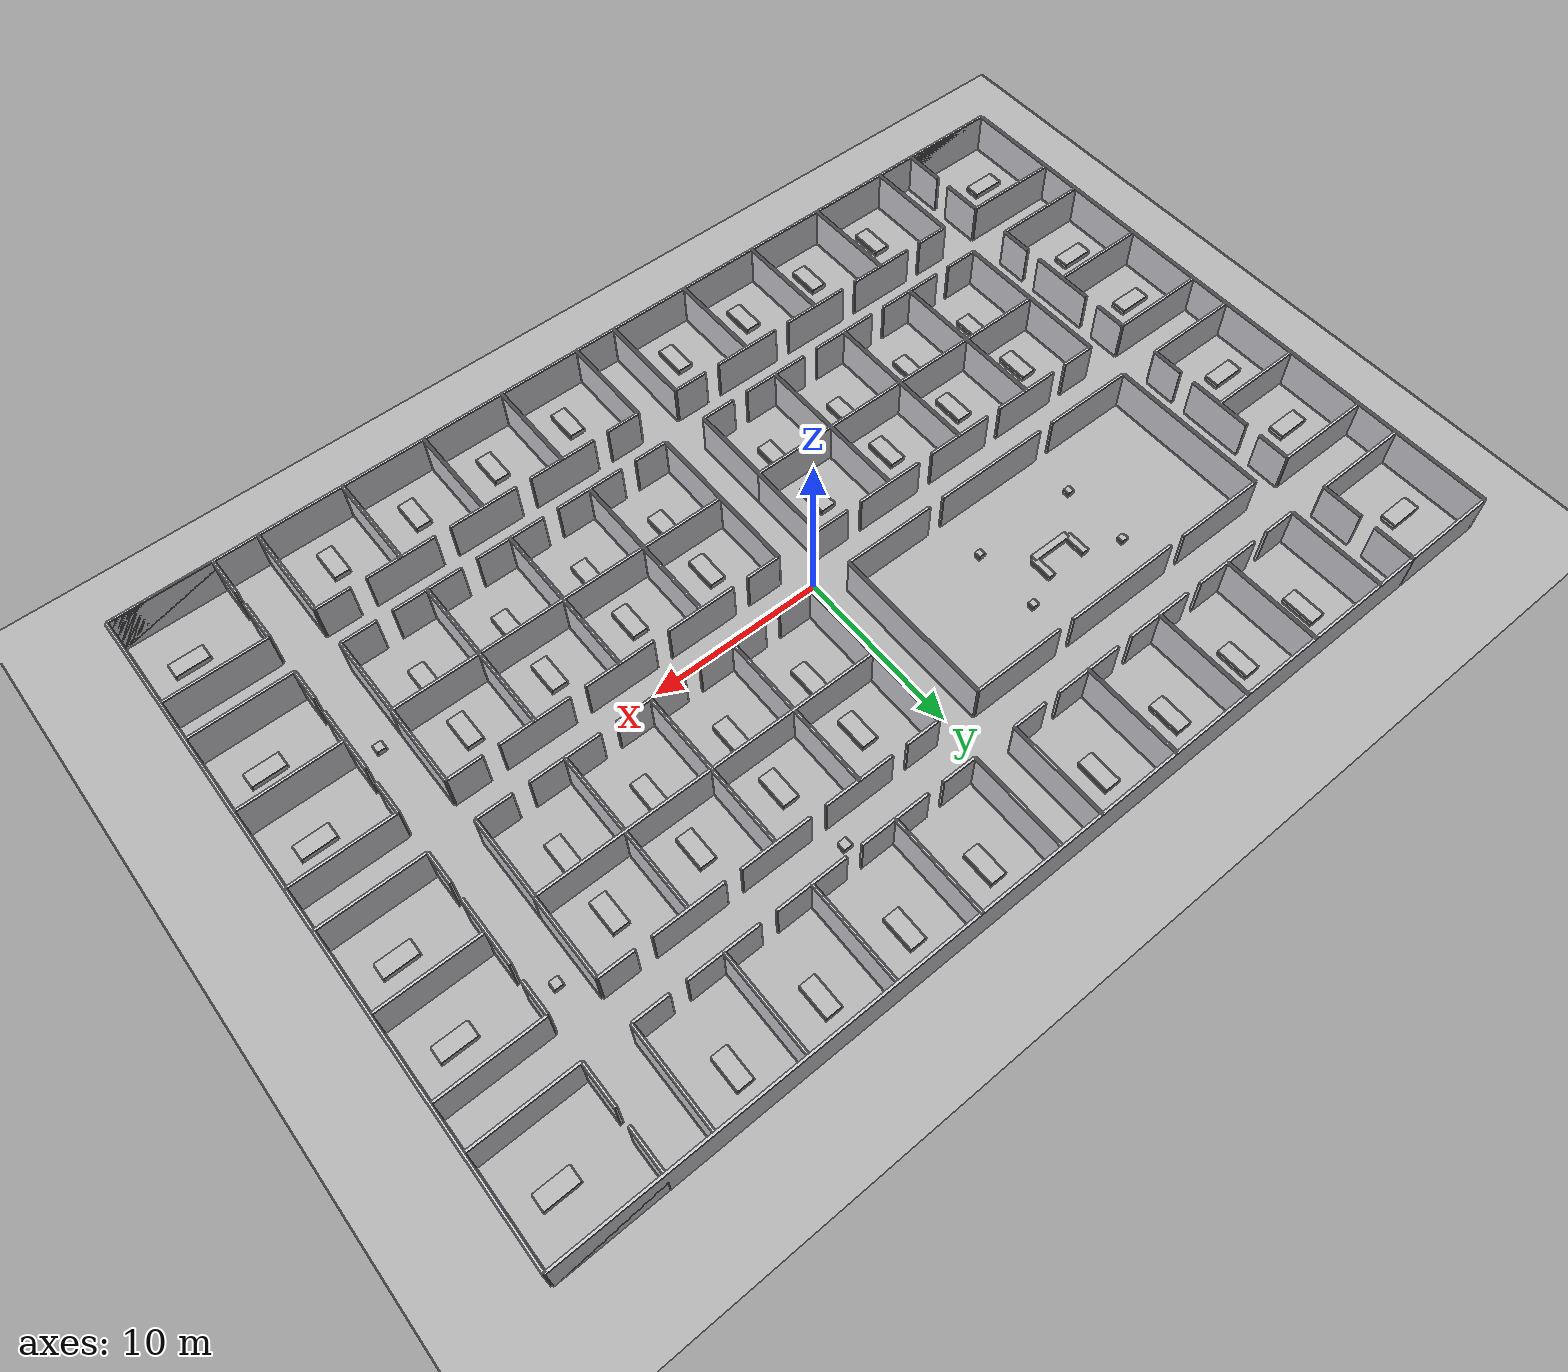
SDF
<?xml version="1.0"?>
<sdf version="1.8">
  <world name="hospital_world">
    <physics name="default_physics" type="dartsim">
      <max_step_size>0.004</max_step_size>
      <real_time_factor>1.0</real_time_factor>
    </physics>

    <plugin filename="gz-sim-physics-system" name="gz::sim::systems::Physics"/>
    <plugin filename="gz-sim-sensors-system" name="gz::sim::systems::Sensors">
      <render_engine>ogre2</render_engine>
    </plugin>
    <plugin filename="gz-sim-scene-broadcaster-system" name="gz::sim::systems::SceneBroadcaster"/>
    <plugin filename="gz-sim-user-commands-system" name="gz::sim::systems::UserCommands"/>

    <light type="directional" name="sun">
      <cast_shadows>false</cast_shadows>
      <pose>0 0 10 0 0 0</pose>
      <diffuse>0.8 0.8 0.8 1</diffuse>
      <direction>-0.5 0.1 -0.9</direction>
    </light>

    <model name="ground_plane">
      <static>true</static>
      <link name="link">
        <collision name="collision">
          <geometry><plane><normal>0 0 1</normal><size>70 50</size></plane></geometry>
        </collision>
        <visual name="visual">
          <geometry><plane><normal>0 0 1</normal><size>70 50</size></plane></geometry>
          <material><ambient>0.7 0.7 0.7 1</ambient><diffuse>0.7 0.7 0.7 1</diffuse></material>
        </visual>
      </link>
    </model>
    <model name="building">
      <static>true</static>
      <link name="link">
        <collision name="c0">
          <pose>0 19 1.25 0 0 0</pose>
          <geometry><box><size>58 0.15 2.5</size></box></geometry>
        </collision>
        <visual name="v0">
          <pose>0 19 1.25 0 0 0</pose>
          <geometry><box><size>58 0.15 2.5</size></box></geometry>
          <material><ambient>0.8 0.8 0.82 1</ambient><diffuse>0.8 0.8 0.82 1</diffuse></material>
        </visual>
        <collision name="c1">
          <pose>0 -19 1.25 0 0 0</pose>
          <geometry><box><size>58 0.15 2.5</size></box></geometry>
        </collision>
        <visual name="v1">
          <pose>0 -19 1.25 0 0 0</pose>
          <geometry><box><size>58 0.15 2.5</size></box></geometry>
          <material><ambient>0.8 0.8 0.82 1</ambient><diffuse>0.8 0.8 0.82 1</diffuse></material>
        </visual>
        <collision name="c2">
          <pose>-29 0 1.25 0 0 0</pose>
          <geometry><box><size>0.15 38 2.5</size></box></geometry>
        </collision>
        <visual name="v2">
          <pose>-29 0 1.25 0 0 0</pose>
          <geometry><box><size>0.15 38 2.5</size></box></geometry>
          <material><ambient>0.8 0.8 0.82 1</ambient><diffuse>0.8 0.8 0.82 1</diffuse></material>
        </visual>
        <collision name="c3">
          <pose>29 0 1.25 0 0 0</pose>
          <geometry><box><size>0.15 38 2.5</size></box></geometry>
        </collision>
        <visual name="v3">
          <pose>29 0 1.25 0 0 0</pose>
          <geometry><box><size>0.15 38 2.5</size></box></geometry>
          <material><ambient>0.8 0.8 0.82 1</ambient><diffuse>0.8 0.8 0.82 1</diffuse></material>
        </visual>
        <collision name="c4">
          <pose>-19.7563 13.25 1.25 0 0 0</pose>
          <geometry><box><size>1.9875 0.15 2.5</size></box></geometry>
        </collision>
        <visual name="v4">
          <pose>-19.7563 13.25 1.25 0 0 0</pose>
          <geometry><box><size>1.9875 0.15 2.5</size></box></geometry>
          <material><ambient>0.8 0.8 0.82 1</ambient><diffuse>0.8 0.8 0.82 1</diffuse></material>
        </visual>
        <collision name="c5">
          <pose>-15.875 13.25 1.25 0 0 0</pose>
          <geometry><box><size>3.975 0.15 2.5</size></box></geometry>
        </collision>
        <visual name="v5">
          <pose>-15.875 13.25 1.25 0 0 0</pose>
          <geometry><box><size>3.975 0.15 2.5</size></box></geometry>
          <material><ambient>0.8 0.8 0.82 1</ambient><diffuse>0.8 0.8 0.82 1</diffuse></material>
        </visual>
        <collision name="c6">
          <pose>-11 13.25 1.25 0 0 0</pose>
          <geometry><box><size>3.975 0.15 2.5</size></box></geometry>
        </collision>
        <visual name="v6">
          <pose>-11 13.25 1.25 0 0 0</pose>
          <geometry><box><size>3.975 0.15 2.5</size></box></geometry>
          <material><ambient>0.8 0.8 0.82 1</ambient><diffuse>0.8 0.8 0.82 1</diffuse></material>
        </visual>
        <collision name="c7">
          <pose>-6.125 13.25 1.25 0 0 0</pose>
          <geometry><box><size>3.975 0.15 2.5</size></box></geometry>
        </collision>
        <visual name="v7">
          <pose>-6.125 13.25 1.25 0 0 0</pose>
          <geometry><box><size>3.975 0.15 2.5</size></box></geometry>
          <material><ambient>0.8 0.8 0.82 1</ambient><diffuse>0.8 0.8 0.82 1</diffuse></material>
        </visual>
        <collision name="c8">
          <pose>-2.24375 13.25 1.25 0 0 0</pose>
          <geometry><box><size>1.9875 0.15 2.5</size></box></geometry>
        </collision>
        <visual name="v8">
          <pose>-2.24375 13.25 1.25 0 0 0</pose>
          <geometry><box><size>1.9875 0.15 2.5</size></box></geometry>
          <material><ambient>0.8 0.8 0.82 1</ambient><diffuse>0.8 0.8 0.82 1</diffuse></material>
        </visual>
        <collision name="c9">
          <pose>-20.75 16.125 1.25 0 0 0</pose>
          <geometry><box><size>0.15 5.75 2.5</size></box></geometry>
        </collision>
        <visual name="v9">
          <pose>-20.75 16.125 1.25 0 0 0</pose>
          <geometry><box><size>0.15 5.75 2.5</size></box></geometry>
          <material><ambient>0.8 0.8 0.82 1</ambient><diffuse>0.8 0.8 0.82 1</diffuse></material>
        </visual>
        <collision name="c10">
          <pose>-15.875 16.125 1.25 0 0 0</pose>
          <geometry><box><size>0.15 5.75 2.5</size></box></geometry>
        </collision>
        <visual name="v10">
          <pose>-15.875 16.125 1.25 0 0 0</pose>
          <geometry><box><size>0.15 5.75 2.5</size></box></geometry>
          <material><ambient>0.8 0.8 0.82 1</ambient><diffuse>0.8 0.8 0.82 1</diffuse></material>
        </visual>
        <collision name="c11">
          <pose>-11 16.125 1.25 0 0 0</pose>
          <geometry><box><size>0.15 5.75 2.5</size></box></geometry>
        </collision>
        <visual name="v11">
          <pose>-11 16.125 1.25 0 0 0</pose>
          <geometry><box><size>0.15 5.75 2.5</size></box></geometry>
          <material><ambient>0.8 0.8 0.82 1</ambient><diffuse>0.8 0.8 0.82 1</diffuse></material>
        </visual>
        <collision name="c12">
          <pose>-6.125 16.125 1.25 0 0 0</pose>
          <geometry><box><size>0.15 5.75 2.5</size></box></geometry>
        </collision>
        <visual name="v12">
          <pose>-6.125 16.125 1.25 0 0 0</pose>
          <geometry><box><size>0.15 5.75 2.5</size></box></geometry>
          <material><ambient>0.8 0.8 0.82 1</ambient><diffuse>0.8 0.8 0.82 1</diffuse></material>
        </visual>
        <collision name="c13">
          <pose>-1.25 16.125 1.25 0 0 0</pose>
          <geometry><box><size>0.15 5.75 2.5</size></box></geometry>
        </collision>
        <visual name="v13">
          <pose>-1.25 16.125 1.25 0 0 0</pose>
          <geometry><box><size>0.15 5.75 2.5</size></box></geometry>
          <material><ambient>0.8 0.8 0.82 1</ambient><diffuse>0.8 0.8 0.82 1</diffuse></material>
        </visual>
        <collision name="c14">
          <pose>2.24375 13.25 1.25 0 0 0</pose>
          <geometry><box><size>1.9875 0.15 2.5</size></box></geometry>
        </collision>
        <visual name="v14">
          <pose>2.24375 13.25 1.25 0 0 0</pose>
          <geometry><box><size>1.9875 0.15 2.5</size></box></geometry>
          <material><ambient>0.8 0.8 0.82 1</ambient><diffuse>0.8 0.8 0.82 1</diffuse></material>
        </visual>
        <collision name="c15">
          <pose>6.125 13.25 1.25 0 0 0</pose>
          <geometry><box><size>3.975 0.15 2.5</size></box></geometry>
        </collision>
        <visual name="v15">
          <pose>6.125 13.25 1.25 0 0 0</pose>
          <geometry><box><size>3.975 0.15 2.5</size></box></geometry>
          <material><ambient>0.8 0.8 0.82 1</ambient><diffuse>0.8 0.8 0.82 1</diffuse></material>
        </visual>
        <collision name="c16">
          <pose>11 13.25 1.25 0 0 0</pose>
          <geometry><box><size>3.975 0.15 2.5</size></box></geometry>
        </collision>
        <visual name="v16">
          <pose>11 13.25 1.25 0 0 0</pose>
          <geometry><box><size>3.975 0.15 2.5</size></box></geometry>
          <material><ambient>0.8 0.8 0.82 1</ambient><diffuse>0.8 0.8 0.82 1</diffuse></material>
        </visual>
        <collision name="c17">
          <pose>15.875 13.25 1.25 0 0 0</pose>
          <geometry><box><size>3.975 0.15 2.5</size></box></geometry>
        </collision>
        <visual name="v17">
          <pose>15.875 13.25 1.25 0 0 0</pose>
          <geometry><box><size>3.975 0.15 2.5</size></box></geometry>
          <material><ambient>0.8 0.8 0.82 1</ambient><diffuse>0.8 0.8 0.82 1</diffuse></material>
        </visual>
        <collision name="c18">
          <pose>19.7563 13.25 1.25 0 0 0</pose>
          <geometry><box><size>1.9875 0.15 2.5</size></box></geometry>
        </collision>
        <visual name="v18">
          <pose>19.7563 13.25 1.25 0 0 0</pose>
          <geometry><box><size>1.9875 0.15 2.5</size></box></geometry>
          <material><ambient>0.8 0.8 0.82 1</ambient><diffuse>0.8 0.8 0.82 1</diffuse></material>
        </visual>
        <collision name="c19">
          <pose>1.25 16.125 1.25 0 0 0</pose>
          <geometry><box><size>0.15 5.75 2.5</size></box></geometry>
        </collision>
        <visual name="v19">
          <pose>1.25 16.125 1.25 0 0 0</pose>
          <geometry><box><size>0.15 5.75 2.5</size></box></geometry>
          <material><ambient>0.8 0.8 0.82 1</ambient><diffuse>0.8 0.8 0.82 1</diffuse></material>
        </visual>
        <collision name="c20">
          <pose>6.125 16.125 1.25 0 0 0</pose>
          <geometry><box><size>0.15 5.75 2.5</size></box></geometry>
        </collision>
        <visual name="v20">
          <pose>6.125 16.125 1.25 0 0 0</pose>
          <geometry><box><size>0.15 5.75 2.5</size></box></geometry>
          <material><ambient>0.8 0.8 0.82 1</ambient><diffuse>0.8 0.8 0.82 1</diffuse></material>
        </visual>
        <collision name="c21">
          <pose>11 16.125 1.25 0 0 0</pose>
          <geometry><box><size>0.15 5.75 2.5</size></box></geometry>
        </collision>
        <visual name="v21">
          <pose>11 16.125 1.25 0 0 0</pose>
          <geometry><box><size>0.15 5.75 2.5</size></box></geometry>
          <material><ambient>0.8 0.8 0.82 1</ambient><diffuse>0.8 0.8 0.82 1</diffuse></material>
        </visual>
        <collision name="c22">
          <pose>15.875 16.125 1.25 0 0 0</pose>
          <geometry><box><size>0.15 5.75 2.5</size></box></geometry>
        </collision>
        <visual name="v22">
          <pose>15.875 16.125 1.25 0 0 0</pose>
          <geometry><box><size>0.15 5.75 2.5</size></box></geometry>
          <material><ambient>0.8 0.8 0.82 1</ambient><diffuse>0.8 0.8 0.82 1</diffuse></material>
        </visual>
        <collision name="c23">
          <pose>20.75 16.125 1.25 0 0 0</pose>
          <geometry><box><size>0.15 5.75 2.5</size></box></geometry>
        </collision>
        <visual name="v23">
          <pose>20.75 16.125 1.25 0 0 0</pose>
          <geometry><box><size>0.15 5.75 2.5</size></box></geometry>
          <material><ambient>0.8 0.8 0.82 1</ambient><diffuse>0.8 0.8 0.82 1</diffuse></material>
        </visual>
        <collision name="c24">
          <pose>-18.05 1.25 1.25 0 0 0</pose>
          <geometry><box><size>5.4 0.15 2.5</size></box></geometry>
        </collision>
        <visual name="v24">
          <pose>-18.05 1.25 1.25 0 0 0</pose>
          <geometry><box><size>5.4 0.15 2.5</size></box></geometry>
          <material><ambient>0.8 0.8 0.82 1</ambient><diffuse>0.8 0.8 0.82 1</diffuse></material>
        </visual>
        <collision name="c25">
          <pose>-11 1.25 1.25 0 0 0</pose>
          <geometry><box><size>6.9 0.15 2.5</size></box></geometry>
        </collision>
        <visual name="v25">
          <pose>-11 1.25 1.25 0 0 0</pose>
          <geometry><box><size>6.9 0.15 2.5</size></box></geometry>
          <material><ambient>0.8 0.8 0.82 1</ambient><diffuse>0.8 0.8 0.82 1</diffuse></material>
        </visual>
        <collision name="c26">
          <pose>-3.95 1.25 1.25 0 0 0</pose>
          <geometry><box><size>5.4 0.15 2.5</size></box></geometry>
        </collision>
        <visual name="v26">
          <pose>-3.95 1.25 1.25 0 0 0</pose>
          <geometry><box><size>5.4 0.15 2.5</size></box></geometry>
          <material><ambient>0.8 0.8 0.82 1</ambient><diffuse>0.8 0.8 0.82 1</diffuse></material>
        </visual>
        <collision name="c27">
          <pose>-18.05 10.75 1.25 0 0 0</pose>
          <geometry><box><size>5.4 0.15 2.5</size></box></geometry>
        </collision>
        <visual name="v27">
          <pose>-18.05 10.75 1.25 0 0 0</pose>
          <geometry><box><size>5.4 0.15 2.5</size></box></geometry>
          <material><ambient>0.8 0.8 0.82 1</ambient><diffuse>0.8 0.8 0.82 1</diffuse></material>
        </visual>
        <collision name="c28">
          <pose>-11 10.75 1.25 0 0 0</pose>
          <geometry><box><size>6.9 0.15 2.5</size></box></geometry>
        </collision>
        <visual name="v28">
          <pose>-11 10.75 1.25 0 0 0</pose>
          <geometry><box><size>6.9 0.15 2.5</size></box></geometry>
          <material><ambient>0.8 0.8 0.82 1</ambient><diffuse>0.8 0.8 0.82 1</diffuse></material>
        </visual>
        <collision name="c29">
          <pose>-3.95 10.75 1.25 0 0 0</pose>
          <geometry><box><size>5.4 0.15 2.5</size></box></geometry>
        </collision>
        <visual name="v29">
          <pose>-3.95 10.75 1.25 0 0 0</pose>
          <geometry><box><size>5.4 0.15 2.5</size></box></geometry>
          <material><ambient>0.8 0.8 0.82 1</ambient><diffuse>0.8 0.8 0.82 1</diffuse></material>
        </visual>
        <collision name="c30">
          <pose>-20.75 6 1.25 0 0 0</pose>
          <geometry><box><size>0.15 9.5 2.5</size></box></geometry>
        </collision>
        <visual name="v30">
          <pose>-20.75 6 1.25 0 0 0</pose>
          <geometry><box><size>0.15 9.5 2.5</size></box></geometry>
          <material><ambient>0.8 0.8 0.82 1</ambient><diffuse>0.8 0.8 0.82 1</diffuse></material>
        </visual>
        <collision name="c31">
          <pose>-1.25 6 1.25 0 0 0</pose>
          <geometry><box><size>0.15 9.5 2.5</size></box></geometry>
        </collision>
        <visual name="v31">
          <pose>-1.25 6 1.25 0 0 0</pose>
          <geometry><box><size>0.15 9.5 2.5</size></box></geometry>
          <material><ambient>0.8 0.8 0.82 1</ambient><diffuse>0.8 0.8 0.82 1</diffuse></material>
        </visual>
        <collision name="c32">
          <pose>2.24375 10.75 1.25 0 0 0</pose>
          <geometry><box><size>1.9875 0.15 2.5</size></box></geometry>
        </collision>
        <visual name="v32">
          <pose>2.24375 10.75 1.25 0 0 0</pose>
          <geometry><box><size>1.9875 0.15 2.5</size></box></geometry>
          <material><ambient>0.8 0.8 0.82 1</ambient><diffuse>0.8 0.8 0.82 1</diffuse></material>
        </visual>
        <collision name="c33">
          <pose>6.125 10.75 1.25 0 0 0</pose>
          <geometry><box><size>3.975 0.15 2.5</size></box></geometry>
        </collision>
        <visual name="v33">
          <pose>6.125 10.75 1.25 0 0 0</pose>
          <geometry><box><size>3.975 0.15 2.5</size></box></geometry>
          <material><ambient>0.8 0.8 0.82 1</ambient><diffuse>0.8 0.8 0.82 1</diffuse></material>
        </visual>
        <collision name="c34">
          <pose>11 10.75 1.25 0 0 0</pose>
          <geometry><box><size>3.975 0.15 2.5</size></box></geometry>
        </collision>
        <visual name="v34">
          <pose>11 10.75 1.25 0 0 0</pose>
          <geometry><box><size>3.975 0.15 2.5</size></box></geometry>
          <material><ambient>0.8 0.8 0.82 1</ambient><diffuse>0.8 0.8 0.82 1</diffuse></material>
        </visual>
        <collision name="c35">
          <pose>15.875 10.75 1.25 0 0 0</pose>
          <geometry><box><size>3.975 0.15 2.5</size></box></geometry>
        </collision>
        <visual name="v35">
          <pose>15.875 10.75 1.25 0 0 0</pose>
          <geometry><box><size>3.975 0.15 2.5</size></box></geometry>
          <material><ambient>0.8 0.8 0.82 1</ambient><diffuse>0.8 0.8 0.82 1</diffuse></material>
        </visual>
        <collision name="c36">
          <pose>19.7563 10.75 1.25 0 0 0</pose>
          <geometry><box><size>1.9875 0.15 2.5</size></box></geometry>
        </collision>
        <visual name="v36">
          <pose>19.7563 10.75 1.25 0 0 0</pose>
          <geometry><box><size>1.9875 0.15 2.5</size></box></geometry>
          <material><ambient>0.8 0.8 0.82 1</ambient><diffuse>0.8 0.8 0.82 1</diffuse></material>
        </visual>
        <collision name="c37">
          <pose>11 6 1.25 0 0 0</pose>
          <geometry><box><size>19.5 0.15 2.5</size></box></geometry>
        </collision>
        <visual name="v37">
          <pose>11 6 1.25 0 0 0</pose>
          <geometry><box><size>19.5 0.15 2.5</size></box></geometry>
          <material><ambient>0.8 0.8 0.82 1</ambient><diffuse>0.8 0.8 0.82 1</diffuse></material>
        </visual>
        <collision name="c38">
          <pose>1.25 8.375 1.25 0 0 0</pose>
          <geometry><box><size>0.15 4.75 2.5</size></box></geometry>
        </collision>
        <visual name="v38">
          <pose>1.25 8.375 1.25 0 0 0</pose>
          <geometry><box><size>0.15 4.75 2.5</size></box></geometry>
          <material><ambient>0.8 0.8 0.82 1</ambient><diffuse>0.8 0.8 0.82 1</diffuse></material>
        </visual>
        <collision name="c39">
          <pose>6.125 8.375 1.25 0 0 0</pose>
          <geometry><box><size>0.15 4.75 2.5</size></box></geometry>
        </collision>
        <visual name="v39">
          <pose>6.125 8.375 1.25 0 0 0</pose>
          <geometry><box><size>0.15 4.75 2.5</size></box></geometry>
          <material><ambient>0.8 0.8 0.82 1</ambient><diffuse>0.8 0.8 0.82 1</diffuse></material>
        </visual>
        <collision name="c40">
          <pose>11 8.375 1.25 0 0 0</pose>
          <geometry><box><size>0.15 4.75 2.5</size></box></geometry>
        </collision>
        <visual name="v40">
          <pose>11 8.375 1.25 0 0 0</pose>
          <geometry><box><size>0.15 4.75 2.5</size></box></geometry>
          <material><ambient>0.8 0.8 0.82 1</ambient><diffuse>0.8 0.8 0.82 1</diffuse></material>
        </visual>
        <collision name="c41">
          <pose>15.875 8.375 1.25 0 0 0</pose>
          <geometry><box><size>0.15 4.75 2.5</size></box></geometry>
        </collision>
        <visual name="v41">
          <pose>15.875 8.375 1.25 0 0 0</pose>
          <geometry><box><size>0.15 4.75 2.5</size></box></geometry>
          <material><ambient>0.8 0.8 0.82 1</ambient><diffuse>0.8 0.8 0.82 1</diffuse></material>
        </visual>
        <collision name="c42">
          <pose>20.75 8.375 1.25 0 0 0</pose>
          <geometry><box><size>0.15 4.75 2.5</size></box></geometry>
        </collision>
        <visual name="v42">
          <pose>20.75 8.375 1.25 0 0 0</pose>
          <geometry><box><size>0.15 4.75 2.5</size></box></geometry>
          <material><ambient>0.8 0.8 0.82 1</ambient><diffuse>0.8 0.8 0.82 1</diffuse></material>
        </visual>
        <collision name="c43">
          <pose>2.24375 1.25 1.25 0 0 0</pose>
          <geometry><box><size>1.9875 0.15 2.5</size></box></geometry>
        </collision>
        <visual name="v43">
          <pose>2.24375 1.25 1.25 0 0 0</pose>
          <geometry><box><size>1.9875 0.15 2.5</size></box></geometry>
          <material><ambient>0.8 0.8 0.82 1</ambient><diffuse>0.8 0.8 0.82 1</diffuse></material>
        </visual>
        <collision name="c44">
          <pose>6.125 1.25 1.25 0 0 0</pose>
          <geometry><box><size>3.975 0.15 2.5</size></box></geometry>
        </collision>
        <visual name="v44">
          <pose>6.125 1.25 1.25 0 0 0</pose>
          <geometry><box><size>3.975 0.15 2.5</size></box></geometry>
          <material><ambient>0.8 0.8 0.82 1</ambient><diffuse>0.8 0.8 0.82 1</diffuse></material>
        </visual>
        <collision name="c45">
          <pose>11 1.25 1.25 0 0 0</pose>
          <geometry><box><size>3.975 0.15 2.5</size></box></geometry>
        </collision>
        <visual name="v45">
          <pose>11 1.25 1.25 0 0 0</pose>
          <geometry><box><size>3.975 0.15 2.5</size></box></geometry>
          <material><ambient>0.8 0.8 0.82 1</ambient><diffuse>0.8 0.8 0.82 1</diffuse></material>
        </visual>
        <collision name="c46">
          <pose>15.875 1.25 1.25 0 0 0</pose>
          <geometry><box><size>3.975 0.15 2.5</size></box></geometry>
        </collision>
        <visual name="v46">
          <pose>15.875 1.25 1.25 0 0 0</pose>
          <geometry><box><size>3.975 0.15 2.5</size></box></geometry>
          <material><ambient>0.8 0.8 0.82 1</ambient><diffuse>0.8 0.8 0.82 1</diffuse></material>
        </visual>
        <collision name="c47">
          <pose>19.7563 1.25 1.25 0 0 0</pose>
          <geometry><box><size>1.9875 0.15 2.5</size></box></geometry>
        </collision>
        <visual name="v47">
          <pose>19.7563 1.25 1.25 0 0 0</pose>
          <geometry><box><size>1.9875 0.15 2.5</size></box></geometry>
          <material><ambient>0.8 0.8 0.82 1</ambient><diffuse>0.8 0.8 0.82 1</diffuse></material>
        </visual>
        <collision name="c48">
          <pose>1.25 3.625 1.25 0 0 0</pose>
          <geometry><box><size>0.15 4.75 2.5</size></box></geometry>
        </collision>
        <visual name="v48">
          <pose>1.25 3.625 1.25 0 0 0</pose>
          <geometry><box><size>0.15 4.75 2.5</size></box></geometry>
          <material><ambient>0.8 0.8 0.82 1</ambient><diffuse>0.8 0.8 0.82 1</diffuse></material>
        </visual>
        <collision name="c49">
          <pose>6.125 3.625 1.25 0 0 0</pose>
          <geometry><box><size>0.15 4.75 2.5</size></box></geometry>
        </collision>
        <visual name="v49">
          <pose>6.125 3.625 1.25 0 0 0</pose>
          <geometry><box><size>0.15 4.75 2.5</size></box></geometry>
          <material><ambient>0.8 0.8 0.82 1</ambient><diffuse>0.8 0.8 0.82 1</diffuse></material>
        </visual>
        <collision name="c50">
          <pose>11 3.625 1.25 0 0 0</pose>
          <geometry><box><size>0.15 4.75 2.5</size></box></geometry>
        </collision>
        <visual name="v50">
          <pose>11 3.625 1.25 0 0 0</pose>
          <geometry><box><size>0.15 4.75 2.5</size></box></geometry>
          <material><ambient>0.8 0.8 0.82 1</ambient><diffuse>0.8 0.8 0.82 1</diffuse></material>
        </visual>
        <collision name="c51">
          <pose>15.875 3.625 1.25 0 0 0</pose>
          <geometry><box><size>0.15 4.75 2.5</size></box></geometry>
        </collision>
        <visual name="v51">
          <pose>15.875 3.625 1.25 0 0 0</pose>
          <geometry><box><size>0.15 4.75 2.5</size></box></geometry>
          <material><ambient>0.8 0.8 0.82 1</ambient><diffuse>0.8 0.8 0.82 1</diffuse></material>
        </visual>
        <collision name="c52">
          <pose>20.75 3.625 1.25 0 0 0</pose>
          <geometry><box><size>0.15 4.75 2.5</size></box></geometry>
        </collision>
        <visual name="v52">
          <pose>20.75 3.625 1.25 0 0 0</pose>
          <geometry><box><size>0.15 4.75 2.5</size></box></geometry>
          <material><ambient>0.8 0.8 0.82 1</ambient><diffuse>0.8 0.8 0.82 1</diffuse></material>
        </visual>
        <collision name="c53">
          <pose>-19.7563 -10.75 1.25 0 0 0</pose>
          <geometry><box><size>1.9875 0.15 2.5</size></box></geometry>
        </collision>
        <visual name="v53">
          <pose>-19.7563 -10.75 1.25 0 0 0</pose>
          <geometry><box><size>1.9875 0.15 2.5</size></box></geometry>
          <material><ambient>0.8 0.8 0.82 1</ambient><diffuse>0.8 0.8 0.82 1</diffuse></material>
        </visual>
        <collision name="c54">
          <pose>-15.875 -10.75 1.25 0 0 0</pose>
          <geometry><box><size>3.975 0.15 2.5</size></box></geometry>
        </collision>
        <visual name="v54">
          <pose>-15.875 -10.75 1.25 0 0 0</pose>
          <geometry><box><size>3.975 0.15 2.5</size></box></geometry>
          <material><ambient>0.8 0.8 0.82 1</ambient><diffuse>0.8 0.8 0.82 1</diffuse></material>
        </visual>
        <collision name="c55">
          <pose>-11 -10.75 1.25 0 0 0</pose>
          <geometry><box><size>3.975 0.15 2.5</size></box></geometry>
        </collision>
        <visual name="v55">
          <pose>-11 -10.75 1.25 0 0 0</pose>
          <geometry><box><size>3.975 0.15 2.5</size></box></geometry>
          <material><ambient>0.8 0.8 0.82 1</ambient><diffuse>0.8 0.8 0.82 1</diffuse></material>
        </visual>
        <collision name="c56">
          <pose>-6.125 -10.75 1.25 0 0 0</pose>
          <geometry><box><size>3.975 0.15 2.5</size></box></geometry>
        </collision>
        <visual name="v56">
          <pose>-6.125 -10.75 1.25 0 0 0</pose>
          <geometry><box><size>3.975 0.15 2.5</size></box></geometry>
          <material><ambient>0.8 0.8 0.82 1</ambient><diffuse>0.8 0.8 0.82 1</diffuse></material>
        </visual>
        <collision name="c57">
          <pose>-2.24375 -10.75 1.25 0 0 0</pose>
          <geometry><box><size>1.9875 0.15 2.5</size></box></geometry>
        </collision>
        <visual name="v57">
          <pose>-2.24375 -10.75 1.25 0 0 0</pose>
          <geometry><box><size>1.9875 0.15 2.5</size></box></geometry>
          <material><ambient>0.8 0.8 0.82 1</ambient><diffuse>0.8 0.8 0.82 1</diffuse></material>
        </visual>
        <collision name="c58">
          <pose>-11 -6 1.25 0 0 0</pose>
          <geometry><box><size>19.5 0.15 2.5</size></box></geometry>
        </collision>
        <visual name="v58">
          <pose>-11 -6 1.25 0 0 0</pose>
          <geometry><box><size>19.5 0.15 2.5</size></box></geometry>
          <material><ambient>0.8 0.8 0.82 1</ambient><diffuse>0.8 0.8 0.82 1</diffuse></material>
        </visual>
        <collision name="c59">
          <pose>-20.75 -8.375 1.25 0 0 0</pose>
          <geometry><box><size>0.15 4.75 2.5</size></box></geometry>
        </collision>
        <visual name="v59">
          <pose>-20.75 -8.375 1.25 0 0 0</pose>
          <geometry><box><size>0.15 4.75 2.5</size></box></geometry>
          <material><ambient>0.8 0.8 0.82 1</ambient><diffuse>0.8 0.8 0.82 1</diffuse></material>
        </visual>
        <collision name="c60">
          <pose>-15.875 -8.375 1.25 0 0 0</pose>
          <geometry><box><size>0.15 4.75 2.5</size></box></geometry>
        </collision>
        <visual name="v60">
          <pose>-15.875 -8.375 1.25 0 0 0</pose>
          <geometry><box><size>0.15 4.75 2.5</size></box></geometry>
          <material><ambient>0.8 0.8 0.82 1</ambient><diffuse>0.8 0.8 0.82 1</diffuse></material>
        </visual>
        <collision name="c61">
          <pose>-11 -8.375 1.25 0 0 0</pose>
          <geometry><box><size>0.15 4.75 2.5</size></box></geometry>
        </collision>
        <visual name="v61">
          <pose>-11 -8.375 1.25 0 0 0</pose>
          <geometry><box><size>0.15 4.75 2.5</size></box></geometry>
          <material><ambient>0.8 0.8 0.82 1</ambient><diffuse>0.8 0.8 0.82 1</diffuse></material>
        </visual>
        <collision name="c62">
          <pose>-6.125 -8.375 1.25 0 0 0</pose>
          <geometry><box><size>0.15 4.75 2.5</size></box></geometry>
        </collision>
        <visual name="v62">
          <pose>-6.125 -8.375 1.25 0 0 0</pose>
          <geometry><box><size>0.15 4.75 2.5</size></box></geometry>
          <material><ambient>0.8 0.8 0.82 1</ambient><diffuse>0.8 0.8 0.82 1</diffuse></material>
        </visual>
        <collision name="c63">
          <pose>-1.25 -8.375 1.25 0 0 0</pose>
          <geometry><box><size>0.15 4.75 2.5</size></box></geometry>
        </collision>
        <visual name="v63">
          <pose>-1.25 -8.375 1.25 0 0 0</pose>
          <geometry><box><size>0.15 4.75 2.5</size></box></geometry>
          <material><ambient>0.8 0.8 0.82 1</ambient><diffuse>0.8 0.8 0.82 1</diffuse></material>
        </visual>
        <collision name="c64">
          <pose>-19.7563 -1.25 1.25 0 0 0</pose>
          <geometry><box><size>1.9875 0.15 2.5</size></box></geometry>
        </collision>
        <visual name="v64">
          <pose>-19.7563 -1.25 1.25 0 0 0</pose>
          <geometry><box><size>1.9875 0.15 2.5</size></box></geometry>
          <material><ambient>0.8 0.8 0.82 1</ambient><diffuse>0.8 0.8 0.82 1</diffuse></material>
        </visual>
        <collision name="c65">
          <pose>-15.875 -1.25 1.25 0 0 0</pose>
          <geometry><box><size>3.975 0.15 2.5</size></box></geometry>
        </collision>
        <visual name="v65">
          <pose>-15.875 -1.25 1.25 0 0 0</pose>
          <geometry><box><size>3.975 0.15 2.5</size></box></geometry>
          <material><ambient>0.8 0.8 0.82 1</ambient><diffuse>0.8 0.8 0.82 1</diffuse></material>
        </visual>
        <collision name="c66">
          <pose>-11 -1.25 1.25 0 0 0</pose>
          <geometry><box><size>3.975 0.15 2.5</size></box></geometry>
        </collision>
        <visual name="v66">
          <pose>-11 -1.25 1.25 0 0 0</pose>
          <geometry><box><size>3.975 0.15 2.5</size></box></geometry>
          <material><ambient>0.8 0.8 0.82 1</ambient><diffuse>0.8 0.8 0.82 1</diffuse></material>
        </visual>
        <collision name="c67">
          <pose>-6.125 -1.25 1.25 0 0 0</pose>
          <geometry><box><size>3.975 0.15 2.5</size></box></geometry>
        </collision>
        <visual name="v67">
          <pose>-6.125 -1.25 1.25 0 0 0</pose>
          <geometry><box><size>3.975 0.15 2.5</size></box></geometry>
          <material><ambient>0.8 0.8 0.82 1</ambient><diffuse>0.8 0.8 0.82 1</diffuse></material>
        </visual>
        <collision name="c68">
          <pose>-2.24375 -1.25 1.25 0 0 0</pose>
          <geometry><box><size>1.9875 0.15 2.5</size></box></geometry>
        </collision>
        <visual name="v68">
          <pose>-2.24375 -1.25 1.25 0 0 0</pose>
          <geometry><box><size>1.9875 0.15 2.5</size></box></geometry>
          <material><ambient>0.8 0.8 0.82 1</ambient><diffuse>0.8 0.8 0.82 1</diffuse></material>
        </visual>
        <collision name="c69">
          <pose>-20.75 -3.625 1.25 0 0 0</pose>
          <geometry><box><size>0.15 4.75 2.5</size></box></geometry>
        </collision>
        <visual name="v69">
          <pose>-20.75 -3.625 1.25 0 0 0</pose>
          <geometry><box><size>0.15 4.75 2.5</size></box></geometry>
          <material><ambient>0.8 0.8 0.82 1</ambient><diffuse>0.8 0.8 0.82 1</diffuse></material>
        </visual>
        <collision name="c70">
          <pose>-15.875 -3.625 1.25 0 0 0</pose>
          <geometry><box><size>0.15 4.75 2.5</size></box></geometry>
        </collision>
        <visual name="v70">
          <pose>-15.875 -3.625 1.25 0 0 0</pose>
          <geometry><box><size>0.15 4.75 2.5</size></box></geometry>
          <material><ambient>0.8 0.8 0.82 1</ambient><diffuse>0.8 0.8 0.82 1</diffuse></material>
        </visual>
        <collision name="c71">
          <pose>-11 -3.625 1.25 0 0 0</pose>
          <geometry><box><size>0.15 4.75 2.5</size></box></geometry>
        </collision>
        <visual name="v71">
          <pose>-11 -3.625 1.25 0 0 0</pose>
          <geometry><box><size>0.15 4.75 2.5</size></box></geometry>
          <material><ambient>0.8 0.8 0.82 1</ambient><diffuse>0.8 0.8 0.82 1</diffuse></material>
        </visual>
        <collision name="c72">
          <pose>-6.125 -3.625 1.25 0 0 0</pose>
          <geometry><box><size>0.15 4.75 2.5</size></box></geometry>
        </collision>
        <visual name="v72">
          <pose>-6.125 -3.625 1.25 0 0 0</pose>
          <geometry><box><size>0.15 4.75 2.5</size></box></geometry>
          <material><ambient>0.8 0.8 0.82 1</ambient><diffuse>0.8 0.8 0.82 1</diffuse></material>
        </visual>
        <collision name="c73">
          <pose>-1.25 -3.625 1.25 0 0 0</pose>
          <geometry><box><size>0.15 4.75 2.5</size></box></geometry>
        </collision>
        <visual name="v73">
          <pose>-1.25 -3.625 1.25 0 0 0</pose>
          <geometry><box><size>0.15 4.75 2.5</size></box></geometry>
          <material><ambient>0.8 0.8 0.82 1</ambient><diffuse>0.8 0.8 0.82 1</diffuse></material>
        </visual>
        <collision name="c74">
          <pose>2.24375 -10.75 1.25 0 0 0</pose>
          <geometry><box><size>1.9875 0.15 2.5</size></box></geometry>
        </collision>
        <visual name="v74">
          <pose>2.24375 -10.75 1.25 0 0 0</pose>
          <geometry><box><size>1.9875 0.15 2.5</size></box></geometry>
          <material><ambient>0.8 0.8 0.82 1</ambient><diffuse>0.8 0.8 0.82 1</diffuse></material>
        </visual>
        <collision name="c75">
          <pose>6.125 -10.75 1.25 0 0 0</pose>
          <geometry><box><size>3.975 0.15 2.5</size></box></geometry>
        </collision>
        <visual name="v75">
          <pose>6.125 -10.75 1.25 0 0 0</pose>
          <geometry><box><size>3.975 0.15 2.5</size></box></geometry>
          <material><ambient>0.8 0.8 0.82 1</ambient><diffuse>0.8 0.8 0.82 1</diffuse></material>
        </visual>
        <collision name="c76">
          <pose>11 -10.75 1.25 0 0 0</pose>
          <geometry><box><size>3.975 0.15 2.5</size></box></geometry>
        </collision>
        <visual name="v76">
          <pose>11 -10.75 1.25 0 0 0</pose>
          <geometry><box><size>3.975 0.15 2.5</size></box></geometry>
          <material><ambient>0.8 0.8 0.82 1</ambient><diffuse>0.8 0.8 0.82 1</diffuse></material>
        </visual>
        <collision name="c77">
          <pose>15.875 -10.75 1.25 0 0 0</pose>
          <geometry><box><size>3.975 0.15 2.5</size></box></geometry>
        </collision>
        <visual name="v77">
          <pose>15.875 -10.75 1.25 0 0 0</pose>
          <geometry><box><size>3.975 0.15 2.5</size></box></geometry>
          <material><ambient>0.8 0.8 0.82 1</ambient><diffuse>0.8 0.8 0.82 1</diffuse></material>
        </visual>
        <collision name="c78">
          <pose>19.7563 -10.75 1.25 0 0 0</pose>
          <geometry><box><size>1.9875 0.15 2.5</size></box></geometry>
        </collision>
        <visual name="v78">
          <pose>19.7563 -10.75 1.25 0 0 0</pose>
          <geometry><box><size>1.9875 0.15 2.5</size></box></geometry>
          <material><ambient>0.8 0.8 0.82 1</ambient><diffuse>0.8 0.8 0.82 1</diffuse></material>
        </visual>
        <collision name="c79">
          <pose>11 -6 1.25 0 0 0</pose>
          <geometry><box><size>19.5 0.15 2.5</size></box></geometry>
        </collision>
        <visual name="v79">
          <pose>11 -6 1.25 0 0 0</pose>
          <geometry><box><size>19.5 0.15 2.5</size></box></geometry>
          <material><ambient>0.8 0.8 0.82 1</ambient><diffuse>0.8 0.8 0.82 1</diffuse></material>
        </visual>
        <collision name="c80">
          <pose>1.25 -8.375 1.25 0 0 0</pose>
          <geometry><box><size>0.15 4.75 2.5</size></box></geometry>
        </collision>
        <visual name="v80">
          <pose>1.25 -8.375 1.25 0 0 0</pose>
          <geometry><box><size>0.15 4.75 2.5</size></box></geometry>
          <material><ambient>0.8 0.8 0.82 1</ambient><diffuse>0.8 0.8 0.82 1</diffuse></material>
        </visual>
        <collision name="c81">
          <pose>6.125 -8.375 1.25 0 0 0</pose>
          <geometry><box><size>0.15 4.75 2.5</size></box></geometry>
        </collision>
        <visual name="v81">
          <pose>6.125 -8.375 1.25 0 0 0</pose>
          <geometry><box><size>0.15 4.75 2.5</size></box></geometry>
          <material><ambient>0.8 0.8 0.82 1</ambient><diffuse>0.8 0.8 0.82 1</diffuse></material>
        </visual>
        <collision name="c82">
          <pose>11 -8.375 1.25 0 0 0</pose>
          <geometry><box><size>0.15 4.75 2.5</size></box></geometry>
        </collision>
        <visual name="v82">
          <pose>11 -8.375 1.25 0 0 0</pose>
          <geometry><box><size>0.15 4.75 2.5</size></box></geometry>
          <material><ambient>0.8 0.8 0.82 1</ambient><diffuse>0.8 0.8 0.82 1</diffuse></material>
        </visual>
        <collision name="c83">
          <pose>15.875 -8.375 1.25 0 0 0</pose>
          <geometry><box><size>0.15 4.75 2.5</size></box></geometry>
        </collision>
        <visual name="v83">
          <pose>15.875 -8.375 1.25 0 0 0</pose>
          <geometry><box><size>0.15 4.75 2.5</size></box></geometry>
          <material><ambient>0.8 0.8 0.82 1</ambient><diffuse>0.8 0.8 0.82 1</diffuse></material>
        </visual>
        <collision name="c84">
          <pose>20.75 -8.375 1.25 0 0 0</pose>
          <geometry><box><size>0.15 4.75 2.5</size></box></geometry>
        </collision>
        <visual name="v84">
          <pose>20.75 -8.375 1.25 0 0 0</pose>
          <geometry><box><size>0.15 4.75 2.5</size></box></geometry>
          <material><ambient>0.8 0.8 0.82 1</ambient><diffuse>0.8 0.8 0.82 1</diffuse></material>
        </visual>
        <collision name="c85">
          <pose>2.24375 -1.25 1.25 0 0 0</pose>
          <geometry><box><size>1.9875 0.15 2.5</size></box></geometry>
        </collision>
        <visual name="v85">
          <pose>2.24375 -1.25 1.25 0 0 0</pose>
          <geometry><box><size>1.9875 0.15 2.5</size></box></geometry>
          <material><ambient>0.8 0.8 0.82 1</ambient><diffuse>0.8 0.8 0.82 1</diffuse></material>
        </visual>
        <collision name="c86">
          <pose>6.125 -1.25 1.25 0 0 0</pose>
          <geometry><box><size>3.975 0.15 2.5</size></box></geometry>
        </collision>
        <visual name="v86">
          <pose>6.125 -1.25 1.25 0 0 0</pose>
          <geometry><box><size>3.975 0.15 2.5</size></box></geometry>
          <material><ambient>0.8 0.8 0.82 1</ambient><diffuse>0.8 0.8 0.82 1</diffuse></material>
        </visual>
        <collision name="c87">
          <pose>11 -1.25 1.25 0 0 0</pose>
          <geometry><box><size>3.975 0.15 2.5</size></box></geometry>
        </collision>
        <visual name="v87">
          <pose>11 -1.25 1.25 0 0 0</pose>
          <geometry><box><size>3.975 0.15 2.5</size></box></geometry>
          <material><ambient>0.8 0.8 0.82 1</ambient><diffuse>0.8 0.8 0.82 1</diffuse></material>
        </visual>
        <collision name="c88">
          <pose>15.875 -1.25 1.25 0 0 0</pose>
          <geometry><box><size>3.975 0.15 2.5</size></box></geometry>
        </collision>
        <visual name="v88">
          <pose>15.875 -1.25 1.25 0 0 0</pose>
          <geometry><box><size>3.975 0.15 2.5</size></box></geometry>
          <material><ambient>0.8 0.8 0.82 1</ambient><diffuse>0.8 0.8 0.82 1</diffuse></material>
        </visual>
        <collision name="c89">
          <pose>19.7563 -1.25 1.25 0 0 0</pose>
          <geometry><box><size>1.9875 0.15 2.5</size></box></geometry>
        </collision>
        <visual name="v89">
          <pose>19.7563 -1.25 1.25 0 0 0</pose>
          <geometry><box><size>1.9875 0.15 2.5</size></box></geometry>
          <material><ambient>0.8 0.8 0.82 1</ambient><diffuse>0.8 0.8 0.82 1</diffuse></material>
        </visual>
        <collision name="c90">
          <pose>1.25 -3.625 1.25 0 0 0</pose>
          <geometry><box><size>0.15 4.75 2.5</size></box></geometry>
        </collision>
        <visual name="v90">
          <pose>1.25 -3.625 1.25 0 0 0</pose>
          <geometry><box><size>0.15 4.75 2.5</size></box></geometry>
          <material><ambient>0.8 0.8 0.82 1</ambient><diffuse>0.8 0.8 0.82 1</diffuse></material>
        </visual>
        <collision name="c91">
          <pose>6.125 -3.625 1.25 0 0 0</pose>
          <geometry><box><size>0.15 4.75 2.5</size></box></geometry>
        </collision>
        <visual name="v91">
          <pose>6.125 -3.625 1.25 0 0 0</pose>
          <geometry><box><size>0.15 4.75 2.5</size></box></geometry>
          <material><ambient>0.8 0.8 0.82 1</ambient><diffuse>0.8 0.8 0.82 1</diffuse></material>
        </visual>
        <collision name="c92">
          <pose>11 -3.625 1.25 0 0 0</pose>
          <geometry><box><size>0.15 4.75 2.5</size></box></geometry>
        </collision>
        <visual name="v92">
          <pose>11 -3.625 1.25 0 0 0</pose>
          <geometry><box><size>0.15 4.75 2.5</size></box></geometry>
          <material><ambient>0.8 0.8 0.82 1</ambient><diffuse>0.8 0.8 0.82 1</diffuse></material>
        </visual>
        <collision name="c93">
          <pose>15.875 -3.625 1.25 0 0 0</pose>
          <geometry><box><size>0.15 4.75 2.5</size></box></geometry>
        </collision>
        <visual name="v93">
          <pose>15.875 -3.625 1.25 0 0 0</pose>
          <geometry><box><size>0.15 4.75 2.5</size></box></geometry>
          <material><ambient>0.8 0.8 0.82 1</ambient><diffuse>0.8 0.8 0.82 1</diffuse></material>
        </visual>
        <collision name="c94">
          <pose>20.75 -3.625 1.25 0 0 0</pose>
          <geometry><box><size>0.15 4.75 2.5</size></box></geometry>
        </collision>
        <visual name="v94">
          <pose>20.75 -3.625 1.25 0 0 0</pose>
          <geometry><box><size>0.15 4.75 2.5</size></box></geometry>
          <material><ambient>0.8 0.8 0.82 1</ambient><diffuse>0.8 0.8 0.82 1</diffuse></material>
        </visual>
        <collision name="c95">
          <pose>-19.7563 -13.25 1.25 0 0 0</pose>
          <geometry><box><size>1.9875 0.15 2.5</size></box></geometry>
        </collision>
        <visual name="v95">
          <pose>-19.7563 -13.25 1.25 0 0 0</pose>
          <geometry><box><size>1.9875 0.15 2.5</size></box></geometry>
          <material><ambient>0.8 0.8 0.82 1</ambient><diffuse>0.8 0.8 0.82 1</diffuse></material>
        </visual>
        <collision name="c96">
          <pose>-15.875 -13.25 1.25 0 0 0</pose>
          <geometry><box><size>3.975 0.15 2.5</size></box></geometry>
        </collision>
        <visual name="v96">
          <pose>-15.875 -13.25 1.25 0 0 0</pose>
          <geometry><box><size>3.975 0.15 2.5</size></box></geometry>
          <material><ambient>0.8 0.8 0.82 1</ambient><diffuse>0.8 0.8 0.82 1</diffuse></material>
        </visual>
        <collision name="c97">
          <pose>-11 -13.25 1.25 0 0 0</pose>
          <geometry><box><size>3.975 0.15 2.5</size></box></geometry>
        </collision>
        <visual name="v97">
          <pose>-11 -13.25 1.25 0 0 0</pose>
          <geometry><box><size>3.975 0.15 2.5</size></box></geometry>
          <material><ambient>0.8 0.8 0.82 1</ambient><diffuse>0.8 0.8 0.82 1</diffuse></material>
        </visual>
        <collision name="c98">
          <pose>-6.125 -13.25 1.25 0 0 0</pose>
          <geometry><box><size>3.975 0.15 2.5</size></box></geometry>
        </collision>
        <visual name="v98">
          <pose>-6.125 -13.25 1.25 0 0 0</pose>
          <geometry><box><size>3.975 0.15 2.5</size></box></geometry>
          <material><ambient>0.8 0.8 0.82 1</ambient><diffuse>0.8 0.8 0.82 1</diffuse></material>
        </visual>
        <collision name="c99">
          <pose>-2.24375 -13.25 1.25 0 0 0</pose>
          <geometry><box><size>1.9875 0.15 2.5</size></box></geometry>
        </collision>
        <visual name="v99">
          <pose>-2.24375 -13.25 1.25 0 0 0</pose>
          <geometry><box><size>1.9875 0.15 2.5</size></box></geometry>
          <material><ambient>0.8 0.8 0.82 1</ambient><diffuse>0.8 0.8 0.82 1</diffuse></material>
        </visual>
        <collision name="c100">
          <pose>-20.75 -16.125 1.25 0 0 0</pose>
          <geometry><box><size>0.15 5.75 2.5</size></box></geometry>
        </collision>
        <visual name="v100">
          <pose>-20.75 -16.125 1.25 0 0 0</pose>
          <geometry><box><size>0.15 5.75 2.5</size></box></geometry>
          <material><ambient>0.8 0.8 0.82 1</ambient><diffuse>0.8 0.8 0.82 1</diffuse></material>
        </visual>
        <collision name="c101">
          <pose>-15.875 -16.125 1.25 0 0 0</pose>
          <geometry><box><size>0.15 5.75 2.5</size></box></geometry>
        </collision>
        <visual name="v101">
          <pose>-15.875 -16.125 1.25 0 0 0</pose>
          <geometry><box><size>0.15 5.75 2.5</size></box></geometry>
          <material><ambient>0.8 0.8 0.82 1</ambient><diffuse>0.8 0.8 0.82 1</diffuse></material>
        </visual>
        <collision name="c102">
          <pose>-11 -16.125 1.25 0 0 0</pose>
          <geometry><box><size>0.15 5.75 2.5</size></box></geometry>
        </collision>
        <visual name="v102">
          <pose>-11 -16.125 1.25 0 0 0</pose>
          <geometry><box><size>0.15 5.75 2.5</size></box></geometry>
          <material><ambient>0.8 0.8 0.82 1</ambient><diffuse>0.8 0.8 0.82 1</diffuse></material>
        </visual>
        <collision name="c103">
          <pose>-6.125 -16.125 1.25 0 0 0</pose>
          <geometry><box><size>0.15 5.75 2.5</size></box></geometry>
        </collision>
        <visual name="v103">
          <pose>-6.125 -16.125 1.25 0 0 0</pose>
          <geometry><box><size>0.15 5.75 2.5</size></box></geometry>
          <material><ambient>0.8 0.8 0.82 1</ambient><diffuse>0.8 0.8 0.82 1</diffuse></material>
        </visual>
        <collision name="c104">
          <pose>-1.25 -16.125 1.25 0 0 0</pose>
          <geometry><box><size>0.15 5.75 2.5</size></box></geometry>
        </collision>
        <visual name="v104">
          <pose>-1.25 -16.125 1.25 0 0 0</pose>
          <geometry><box><size>0.15 5.75 2.5</size></box></geometry>
          <material><ambient>0.8 0.8 0.82 1</ambient><diffuse>0.8 0.8 0.82 1</diffuse></material>
        </visual>
        <collision name="c105">
          <pose>2.24375 -13.25 1.25 0 0 0</pose>
          <geometry><box><size>1.9875 0.15 2.5</size></box></geometry>
        </collision>
        <visual name="v105">
          <pose>2.24375 -13.25 1.25 0 0 0</pose>
          <geometry><box><size>1.9875 0.15 2.5</size></box></geometry>
          <material><ambient>0.8 0.8 0.82 1</ambient><diffuse>0.8 0.8 0.82 1</diffuse></material>
        </visual>
        <collision name="c106">
          <pose>6.125 -13.25 1.25 0 0 0</pose>
          <geometry><box><size>3.975 0.15 2.5</size></box></geometry>
        </collision>
        <visual name="v106">
          <pose>6.125 -13.25 1.25 0 0 0</pose>
          <geometry><box><size>3.975 0.15 2.5</size></box></geometry>
          <material><ambient>0.8 0.8 0.82 1</ambient><diffuse>0.8 0.8 0.82 1</diffuse></material>
        </visual>
        <collision name="c107">
          <pose>11 -13.25 1.25 0 0 0</pose>
          <geometry><box><size>3.975 0.15 2.5</size></box></geometry>
        </collision>
        <visual name="v107">
          <pose>11 -13.25 1.25 0 0 0</pose>
          <geometry><box><size>3.975 0.15 2.5</size></box></geometry>
          <material><ambient>0.8 0.8 0.82 1</ambient><diffuse>0.8 0.8 0.82 1</diffuse></material>
        </visual>
        <collision name="c108">
          <pose>15.875 -13.25 1.25 0 0 0</pose>
          <geometry><box><size>3.975 0.15 2.5</size></box></geometry>
        </collision>
        <visual name="v108">
          <pose>15.875 -13.25 1.25 0 0 0</pose>
          <geometry><box><size>3.975 0.15 2.5</size></box></geometry>
          <material><ambient>0.8 0.8 0.82 1</ambient><diffuse>0.8 0.8 0.82 1</diffuse></material>
        </visual>
        <collision name="c109">
          <pose>19.7563 -13.25 1.25 0 0 0</pose>
          <geometry><box><size>1.9875 0.15 2.5</size></box></geometry>
        </collision>
        <visual name="v109">
          <pose>19.7563 -13.25 1.25 0 0 0</pose>
          <geometry><box><size>1.9875 0.15 2.5</size></box></geometry>
          <material><ambient>0.8 0.8 0.82 1</ambient><diffuse>0.8 0.8 0.82 1</diffuse></material>
        </visual>
        <collision name="c110">
          <pose>1.25 -16.125 1.25 0 0 0</pose>
          <geometry><box><size>0.15 5.75 2.5</size></box></geometry>
        </collision>
        <visual name="v110">
          <pose>1.25 -16.125 1.25 0 0 0</pose>
          <geometry><box><size>0.15 5.75 2.5</size></box></geometry>
          <material><ambient>0.8 0.8 0.82 1</ambient><diffuse>0.8 0.8 0.82 1</diffuse></material>
        </visual>
        <collision name="c111">
          <pose>6.125 -16.125 1.25 0 0 0</pose>
          <geometry><box><size>0.15 5.75 2.5</size></box></geometry>
        </collision>
        <visual name="v111">
          <pose>6.125 -16.125 1.25 0 0 0</pose>
          <geometry><box><size>0.15 5.75 2.5</size></box></geometry>
          <material><ambient>0.8 0.8 0.82 1</ambient><diffuse>0.8 0.8 0.82 1</diffuse></material>
        </visual>
        <collision name="c112">
          <pose>11 -16.125 1.25 0 0 0</pose>
          <geometry><box><size>0.15 5.75 2.5</size></box></geometry>
        </collision>
        <visual name="v112">
          <pose>11 -16.125 1.25 0 0 0</pose>
          <geometry><box><size>0.15 5.75 2.5</size></box></geometry>
          <material><ambient>0.8 0.8 0.82 1</ambient><diffuse>0.8 0.8 0.82 1</diffuse></material>
        </visual>
        <collision name="c113">
          <pose>15.875 -16.125 1.25 0 0 0</pose>
          <geometry><box><size>0.15 5.75 2.5</size></box></geometry>
        </collision>
        <visual name="v113">
          <pose>15.875 -16.125 1.25 0 0 0</pose>
          <geometry><box><size>0.15 5.75 2.5</size></box></geometry>
          <material><ambient>0.8 0.8 0.82 1</ambient><diffuse>0.8 0.8 0.82 1</diffuse></material>
        </visual>
        <collision name="c114">
          <pose>20.75 -16.125 1.25 0 0 0</pose>
          <geometry><box><size>0.15 5.75 2.5</size></box></geometry>
        </collision>
        <visual name="v114">
          <pose>20.75 -16.125 1.25 0 0 0</pose>
          <geometry><box><size>0.15 5.75 2.5</size></box></geometry>
          <material><ambient>0.8 0.8 0.82 1</ambient><diffuse>0.8 0.8 0.82 1</diffuse></material>
        </visual>
        <collision name="c115">
          <pose>-23.25 14.4625 1.25 0 0 0</pose>
          <geometry><box><size>0.15 2.425 2.5</size></box></geometry>
        </collision>
        <visual name="v115">
          <pose>-23.25 14.4625 1.25 0 0 0</pose>
          <geometry><box><size>0.15 2.425 2.5</size></box></geometry>
          <material><ambient>0.8 0.8 0.82 1</ambient><diffuse>0.8 0.8 0.82 1</diffuse></material>
        </visual>
        <collision name="c116">
          <pose>-23.25 17.7875 1.25 0 0 0</pose>
          <geometry><box><size>0.15 2.425 2.5</size></box></geometry>
        </collision>
        <visual name="v116">
          <pose>-23.25 17.7875 1.25 0 0 0</pose>
          <geometry><box><size>0.15 2.425 2.5</size></box></geometry>
          <material><ambient>0.8 0.8 0.82 1</ambient><diffuse>0.8 0.8 0.82 1</diffuse></material>
        </visual>
        <collision name="c117">
          <pose>-26.125 13.25 1.25 0 0 0</pose>
          <geometry><box><size>5.75 0.15 2.5</size></box></geometry>
        </collision>
        <visual name="v117">
          <pose>-26.125 13.25 1.25 0 0 0</pose>
          <geometry><box><size>5.75 0.15 2.5</size></box></geometry>
          <material><ambient>0.8 0.8 0.82 1</ambient><diffuse>0.8 0.8 0.82 1</diffuse></material>
        </visual>
        <collision name="c118">
          <pose>-26.125 19 1.25 0 0 0</pose>
          <geometry><box><size>5.75 0.15 2.5</size></box></geometry>
        </collision>
        <visual name="v118">
          <pose>-26.125 19 1.25 0 0 0</pose>
          <geometry><box><size>5.75 0.15 2.5</size></box></geometry>
          <material><ambient>0.8 0.8 0.82 1</ambient><diffuse>0.8 0.8 0.82 1</diffuse></material>
        </visual>
        <collision name="c119">
          <pose>23.25 14.4625 1.25 0 0 0</pose>
          <geometry><box><size>0.15 2.425 2.5</size></box></geometry>
        </collision>
        <visual name="v119">
          <pose>23.25 14.4625 1.25 0 0 0</pose>
          <geometry><box><size>0.15 2.425 2.5</size></box></geometry>
          <material><ambient>0.8 0.8 0.82 1</ambient><diffuse>0.8 0.8 0.82 1</diffuse></material>
        </visual>
        <collision name="c120">
          <pose>23.25 17.7875 1.25 0 0 0</pose>
          <geometry><box><size>0.15 2.425 2.5</size></box></geometry>
        </collision>
        <visual name="v120">
          <pose>23.25 17.7875 1.25 0 0 0</pose>
          <geometry><box><size>0.15 2.425 2.5</size></box></geometry>
          <material><ambient>0.8 0.8 0.82 1</ambient><diffuse>0.8 0.8 0.82 1</diffuse></material>
        </visual>
        <collision name="c121">
          <pose>26.125 13.25 1.25 0 0 0</pose>
          <geometry><box><size>5.75 0.15 2.5</size></box></geometry>
        </collision>
        <visual name="v121">
          <pose>26.125 13.25 1.25 0 0 0</pose>
          <geometry><box><size>5.75 0.15 2.5</size></box></geometry>
          <material><ambient>0.8 0.8 0.82 1</ambient><diffuse>0.8 0.8 0.82 1</diffuse></material>
        </visual>
        <collision name="c122">
          <pose>26.125 19 1.25 0 0 0</pose>
          <geometry><box><size>5.75 0.15 2.5</size></box></geometry>
        </collision>
        <visual name="v122">
          <pose>26.125 19 1.25 0 0 0</pose>
          <geometry><box><size>5.75 0.15 2.5</size></box></geometry>
          <material><ambient>0.8 0.8 0.82 1</ambient><diffuse>0.8 0.8 0.82 1</diffuse></material>
        </visual>
        <collision name="c123">
          <pose>-23.25 2.2125 1.25 0 0 0</pose>
          <geometry><box><size>0.15 1.925 2.5</size></box></geometry>
        </collision>
        <visual name="v123">
          <pose>-23.25 2.2125 1.25 0 0 0</pose>
          <geometry><box><size>0.15 1.925 2.5</size></box></geometry>
          <material><ambient>0.8 0.8 0.82 1</ambient><diffuse>0.8 0.8 0.82 1</diffuse></material>
        </visual>
        <collision name="c124">
          <pose>-23.25 6 1.25 0 0 0</pose>
          <geometry><box><size>0.15 3.85 2.5</size></box></geometry>
        </collision>
        <visual name="v124">
          <pose>-23.25 6 1.25 0 0 0</pose>
          <geometry><box><size>0.15 3.85 2.5</size></box></geometry>
          <material><ambient>0.8 0.8 0.82 1</ambient><diffuse>0.8 0.8 0.82 1</diffuse></material>
        </visual>
        <collision name="c125">
          <pose>-23.25 9.7875 1.25 0 0 0</pose>
          <geometry><box><size>0.15 1.925 2.5</size></box></geometry>
        </collision>
        <visual name="v125">
          <pose>-23.25 9.7875 1.25 0 0 0</pose>
          <geometry><box><size>0.15 1.925 2.5</size></box></geometry>
          <material><ambient>0.8 0.8 0.82 1</ambient><diffuse>0.8 0.8 0.82 1</diffuse></material>
        </visual>
        <collision name="c126">
          <pose>-26.125 1.25 1.25 0 0 0</pose>
          <geometry><box><size>5.75 0.15 2.5</size></box></geometry>
        </collision>
        <visual name="v126">
          <pose>-26.125 1.25 1.25 0 0 0</pose>
          <geometry><box><size>5.75 0.15 2.5</size></box></geometry>
          <material><ambient>0.8 0.8 0.82 1</ambient><diffuse>0.8 0.8 0.82 1</diffuse></material>
        </visual>
        <collision name="c127">
          <pose>-26.125 6 1.25 0 0 0</pose>
          <geometry><box><size>5.75 0.15 2.5</size></box></geometry>
        </collision>
        <visual name="v127">
          <pose>-26.125 6 1.25 0 0 0</pose>
          <geometry><box><size>5.75 0.15 2.5</size></box></geometry>
          <material><ambient>0.8 0.8 0.82 1</ambient><diffuse>0.8 0.8 0.82 1</diffuse></material>
        </visual>
        <collision name="c128">
          <pose>-26.125 10.75 1.25 0 0 0</pose>
          <geometry><box><size>5.75 0.15 2.5</size></box></geometry>
        </collision>
        <visual name="v128">
          <pose>-26.125 10.75 1.25 0 0 0</pose>
          <geometry><box><size>5.75 0.15 2.5</size></box></geometry>
          <material><ambient>0.8 0.8 0.82 1</ambient><diffuse>0.8 0.8 0.82 1</diffuse></material>
        </visual>
        <collision name="c129">
          <pose>23.25 2.2125 1.25 0 0 0</pose>
          <geometry><box><size>0.15 1.925 2.5</size></box></geometry>
        </collision>
        <visual name="v129">
          <pose>23.25 2.2125 1.25 0 0 0</pose>
          <geometry><box><size>0.15 1.925 2.5</size></box></geometry>
          <material><ambient>0.8 0.8 0.82 1</ambient><diffuse>0.8 0.8 0.82 1</diffuse></material>
        </visual>
        <collision name="c130">
          <pose>23.25 6 1.25 0 0 0</pose>
          <geometry><box><size>0.15 3.85 2.5</size></box></geometry>
        </collision>
        <visual name="v130">
          <pose>23.25 6 1.25 0 0 0</pose>
          <geometry><box><size>0.15 3.85 2.5</size></box></geometry>
          <material><ambient>0.8 0.8 0.82 1</ambient><diffuse>0.8 0.8 0.82 1</diffuse></material>
        </visual>
        <collision name="c131">
          <pose>23.25 9.7875 1.25 0 0 0</pose>
          <geometry><box><size>0.15 1.925 2.5</size></box></geometry>
        </collision>
        <visual name="v131">
          <pose>23.25 9.7875 1.25 0 0 0</pose>
          <geometry><box><size>0.15 1.925 2.5</size></box></geometry>
          <material><ambient>0.8 0.8 0.82 1</ambient><diffuse>0.8 0.8 0.82 1</diffuse></material>
        </visual>
        <collision name="c132">
          <pose>26.125 1.25 1.25 0 0 0</pose>
          <geometry><box><size>5.75 0.15 2.5</size></box></geometry>
        </collision>
        <visual name="v132">
          <pose>26.125 1.25 1.25 0 0 0</pose>
          <geometry><box><size>5.75 0.15 2.5</size></box></geometry>
          <material><ambient>0.8 0.8 0.82 1</ambient><diffuse>0.8 0.8 0.82 1</diffuse></material>
        </visual>
        <collision name="c133">
          <pose>26.125 6 1.25 0 0 0</pose>
          <geometry><box><size>5.75 0.15 2.5</size></box></geometry>
        </collision>
        <visual name="v133">
          <pose>26.125 6 1.25 0 0 0</pose>
          <geometry><box><size>5.75 0.15 2.5</size></box></geometry>
          <material><ambient>0.8 0.8 0.82 1</ambient><diffuse>0.8 0.8 0.82 1</diffuse></material>
        </visual>
        <collision name="c134">
          <pose>26.125 10.75 1.25 0 0 0</pose>
          <geometry><box><size>5.75 0.15 2.5</size></box></geometry>
        </collision>
        <visual name="v134">
          <pose>26.125 10.75 1.25 0 0 0</pose>
          <geometry><box><size>5.75 0.15 2.5</size></box></geometry>
          <material><ambient>0.8 0.8 0.82 1</ambient><diffuse>0.8 0.8 0.82 1</diffuse></material>
        </visual>
        <collision name="c135">
          <pose>-23.25 -9.7875 1.25 0 0 0</pose>
          <geometry><box><size>0.15 1.925 2.5</size></box></geometry>
        </collision>
        <visual name="v135">
          <pose>-23.25 -9.7875 1.25 0 0 0</pose>
          <geometry><box><size>0.15 1.925 2.5</size></box></geometry>
          <material><ambient>0.8 0.8 0.82 1</ambient><diffuse>0.8 0.8 0.82 1</diffuse></material>
        </visual>
        <collision name="c136">
          <pose>-23.25 -6 1.25 0 0 0</pose>
          <geometry><box><size>0.15 3.85 2.5</size></box></geometry>
        </collision>
        <visual name="v136">
          <pose>-23.25 -6 1.25 0 0 0</pose>
          <geometry><box><size>0.15 3.85 2.5</size></box></geometry>
          <material><ambient>0.8 0.8 0.82 1</ambient><diffuse>0.8 0.8 0.82 1</diffuse></material>
        </visual>
        <collision name="c137">
          <pose>-23.25 -2.2125 1.25 0 0 0</pose>
          <geometry><box><size>0.15 1.925 2.5</size></box></geometry>
        </collision>
        <visual name="v137">
          <pose>-23.25 -2.2125 1.25 0 0 0</pose>
          <geometry><box><size>0.15 1.925 2.5</size></box></geometry>
          <material><ambient>0.8 0.8 0.82 1</ambient><diffuse>0.8 0.8 0.82 1</diffuse></material>
        </visual>
        <collision name="c138">
          <pose>-26.125 -10.75 1.25 0 0 0</pose>
          <geometry><box><size>5.75 0.15 2.5</size></box></geometry>
        </collision>
        <visual name="v138">
          <pose>-26.125 -10.75 1.25 0 0 0</pose>
          <geometry><box><size>5.75 0.15 2.5</size></box></geometry>
          <material><ambient>0.8 0.8 0.82 1</ambient><diffuse>0.8 0.8 0.82 1</diffuse></material>
        </visual>
        <collision name="c139">
          <pose>-26.125 -6 1.25 0 0 0</pose>
          <geometry><box><size>5.75 0.15 2.5</size></box></geometry>
        </collision>
        <visual name="v139">
          <pose>-26.125 -6 1.25 0 0 0</pose>
          <geometry><box><size>5.75 0.15 2.5</size></box></geometry>
          <material><ambient>0.8 0.8 0.82 1</ambient><diffuse>0.8 0.8 0.82 1</diffuse></material>
        </visual>
        <collision name="c140">
          <pose>-26.125 -1.25 1.25 0 0 0</pose>
          <geometry><box><size>5.75 0.15 2.5</size></box></geometry>
        </collision>
        <visual name="v140">
          <pose>-26.125 -1.25 1.25 0 0 0</pose>
          <geometry><box><size>5.75 0.15 2.5</size></box></geometry>
          <material><ambient>0.8 0.8 0.82 1</ambient><diffuse>0.8 0.8 0.82 1</diffuse></material>
        </visual>
        <collision name="c141">
          <pose>23.25 -9.7875 1.25 0 0 0</pose>
          <geometry><box><size>0.15 1.925 2.5</size></box></geometry>
        </collision>
        <visual name="v141">
          <pose>23.25 -9.7875 1.25 0 0 0</pose>
          <geometry><box><size>0.15 1.925 2.5</size></box></geometry>
          <material><ambient>0.8 0.8 0.82 1</ambient><diffuse>0.8 0.8 0.82 1</diffuse></material>
        </visual>
        <collision name="c142">
          <pose>23.25 -6 1.25 0 0 0</pose>
          <geometry><box><size>0.15 3.85 2.5</size></box></geometry>
        </collision>
        <visual name="v142">
          <pose>23.25 -6 1.25 0 0 0</pose>
          <geometry><box><size>0.15 3.85 2.5</size></box></geometry>
          <material><ambient>0.8 0.8 0.82 1</ambient><diffuse>0.8 0.8 0.82 1</diffuse></material>
        </visual>
        <collision name="c143">
          <pose>23.25 -2.2125 1.25 0 0 0</pose>
          <geometry><box><size>0.15 1.925 2.5</size></box></geometry>
        </collision>
        <visual name="v143">
          <pose>23.25 -2.2125 1.25 0 0 0</pose>
          <geometry><box><size>0.15 1.925 2.5</size></box></geometry>
          <material><ambient>0.8 0.8 0.82 1</ambient><diffuse>0.8 0.8 0.82 1</diffuse></material>
        </visual>
        <collision name="c144">
          <pose>26.125 -10.75 1.25 0 0 0</pose>
          <geometry><box><size>5.75 0.15 2.5</size></box></geometry>
        </collision>
        <visual name="v144">
          <pose>26.125 -10.75 1.25 0 0 0</pose>
          <geometry><box><size>5.75 0.15 2.5</size></box></geometry>
          <material><ambient>0.8 0.8 0.82 1</ambient><diffuse>0.8 0.8 0.82 1</diffuse></material>
        </visual>
        <collision name="c145">
          <pose>26.125 -6 1.25 0 0 0</pose>
          <geometry><box><size>5.75 0.15 2.5</size></box></geometry>
        </collision>
        <visual name="v145">
          <pose>26.125 -6 1.25 0 0 0</pose>
          <geometry><box><size>5.75 0.15 2.5</size></box></geometry>
          <material><ambient>0.8 0.8 0.82 1</ambient><diffuse>0.8 0.8 0.82 1</diffuse></material>
        </visual>
        <collision name="c146">
          <pose>26.125 -1.25 1.25 0 0 0</pose>
          <geometry><box><size>5.75 0.15 2.5</size></box></geometry>
        </collision>
        <visual name="v146">
          <pose>26.125 -1.25 1.25 0 0 0</pose>
          <geometry><box><size>5.75 0.15 2.5</size></box></geometry>
          <material><ambient>0.8 0.8 0.82 1</ambient><diffuse>0.8 0.8 0.82 1</diffuse></material>
        </visual>
        <collision name="c147">
          <pose>-23.25 -17.7875 1.25 0 0 0</pose>
          <geometry><box><size>0.15 2.425 2.5</size></box></geometry>
        </collision>
        <visual name="v147">
          <pose>-23.25 -17.7875 1.25 0 0 0</pose>
          <geometry><box><size>0.15 2.425 2.5</size></box></geometry>
          <material><ambient>0.8 0.8 0.82 1</ambient><diffuse>0.8 0.8 0.82 1</diffuse></material>
        </visual>
        <collision name="c148">
          <pose>-23.25 -14.4625 1.25 0 0 0</pose>
          <geometry><box><size>0.15 2.425 2.5</size></box></geometry>
        </collision>
        <visual name="v148">
          <pose>-23.25 -14.4625 1.25 0 0 0</pose>
          <geometry><box><size>0.15 2.425 2.5</size></box></geometry>
          <material><ambient>0.8 0.8 0.82 1</ambient><diffuse>0.8 0.8 0.82 1</diffuse></material>
        </visual>
        <collision name="c149">
          <pose>-26.125 -19 1.25 0 0 0</pose>
          <geometry><box><size>5.75 0.15 2.5</size></box></geometry>
        </collision>
        <visual name="v149">
          <pose>-26.125 -19 1.25 0 0 0</pose>
          <geometry><box><size>5.75 0.15 2.5</size></box></geometry>
          <material><ambient>0.8 0.8 0.82 1</ambient><diffuse>0.8 0.8 0.82 1</diffuse></material>
        </visual>
        <collision name="c150">
          <pose>-26.125 -13.25 1.25 0 0 0</pose>
          <geometry><box><size>5.75 0.15 2.5</size></box></geometry>
        </collision>
        <visual name="v150">
          <pose>-26.125 -13.25 1.25 0 0 0</pose>
          <geometry><box><size>5.75 0.15 2.5</size></box></geometry>
          <material><ambient>0.8 0.8 0.82 1</ambient><diffuse>0.8 0.8 0.82 1</diffuse></material>
        </visual>
        <collision name="c151">
          <pose>23.25 -17.7875 1.25 0 0 0</pose>
          <geometry><box><size>0.15 2.425 2.5</size></box></geometry>
        </collision>
        <visual name="v151">
          <pose>23.25 -17.7875 1.25 0 0 0</pose>
          <geometry><box><size>0.15 2.425 2.5</size></box></geometry>
          <material><ambient>0.8 0.8 0.82 1</ambient><diffuse>0.8 0.8 0.82 1</diffuse></material>
        </visual>
        <collision name="c152">
          <pose>23.25 -14.4625 1.25 0 0 0</pose>
          <geometry><box><size>0.15 2.425 2.5</size></box></geometry>
        </collision>
        <visual name="v152">
          <pose>23.25 -14.4625 1.25 0 0 0</pose>
          <geometry><box><size>0.15 2.425 2.5</size></box></geometry>
          <material><ambient>0.8 0.8 0.82 1</ambient><diffuse>0.8 0.8 0.82 1</diffuse></material>
        </visual>
        <collision name="c153">
          <pose>26.125 -19 1.25 0 0 0</pose>
          <geometry><box><size>5.75 0.15 2.5</size></box></geometry>
        </collision>
        <visual name="v153">
          <pose>26.125 -19 1.25 0 0 0</pose>
          <geometry><box><size>5.75 0.15 2.5</size></box></geometry>
          <material><ambient>0.8 0.8 0.82 1</ambient><diffuse>0.8 0.8 0.82 1</diffuse></material>
        </visual>
        <collision name="c154">
          <pose>26.125 -13.25 1.25 0 0 0</pose>
          <geometry><box><size>5.75 0.15 2.5</size></box></geometry>
        </collision>
        <visual name="v154">
          <pose>26.125 -13.25 1.25 0 0 0</pose>
          <geometry><box><size>5.75 0.15 2.5</size></box></geometry>
          <material><ambient>0.8 0.8 0.82 1</ambient><diffuse>0.8 0.8 0.82 1</diffuse></material>
        </visual>
      </link>
    </model>
    <model name="furniture">
      <static>true</static>
      <link name="link">
        <collision name="c0">
          <pose>-18.3125 16.815 0.15 0 0 0</pose>
          <geometry><box><size>0.9 1.9 0.3</size></box></geometry>
        </collision>
        <visual name="v0">
          <pose>-18.3125 16.815 0.15 0 0 0</pose>
          <geometry><box><size>0.9 1.9 0.3</size></box></geometry>
        </visual>
        <collision name="c1">
          <pose>-13.4375 16.815 0.15 0 0 0</pose>
          <geometry><box><size>0.9 1.9 0.3</size></box></geometry>
        </collision>
        <visual name="v1">
          <pose>-13.4375 16.815 0.15 0 0 0</pose>
          <geometry><box><size>0.9 1.9 0.3</size></box></geometry>
        </visual>
        <collision name="c2">
          <pose>-8.5625 16.815 0.15 0 0 0</pose>
          <geometry><box><size>0.9 1.9 0.3</size></box></geometry>
        </collision>
        <visual name="v2">
          <pose>-8.5625 16.815 0.15 0 0 0</pose>
          <geometry><box><size>0.9 1.9 0.3</size></box></geometry>
        </visual>
        <collision name="c3">
          <pose>-3.6875 16.815 0.15 0 0 0</pose>
          <geometry><box><size>0.9 1.9 0.3</size></box></geometry>
        </collision>
        <visual name="v3">
          <pose>-3.6875 16.815 0.15 0 0 0</pose>
          <geometry><box><size>0.9 1.9 0.3</size></box></geometry>
        </visual>
        <collision name="c4">
          <pose>3.6875 16.815 0.15 0 0 0</pose>
          <geometry><box><size>0.9 1.9 0.3</size></box></geometry>
        </collision>
        <visual name="v4">
          <pose>3.6875 16.815 0.15 0 0 0</pose>
          <geometry><box><size>0.9 1.9 0.3</size></box></geometry>
        </visual>
        <collision name="c5">
          <pose>8.5625 16.815 0.15 0 0 0</pose>
          <geometry><box><size>0.9 1.9 0.3</size></box></geometry>
        </collision>
        <visual name="v5">
          <pose>8.5625 16.815 0.15 0 0 0</pose>
          <geometry><box><size>0.9 1.9 0.3</size></box></geometry>
        </visual>
        <collision name="c6">
          <pose>13.4375 16.815 0.15 0 0 0</pose>
          <geometry><box><size>0.9 1.9 0.3</size></box></geometry>
        </collision>
        <visual name="v6">
          <pose>13.4375 16.815 0.15 0 0 0</pose>
          <geometry><box><size>0.9 1.9 0.3</size></box></geometry>
        </visual>
        <collision name="c7">
          <pose>18.3125 16.815 0.15 0 0 0</pose>
          <geometry><box><size>0.9 1.9 0.3</size></box></geometry>
        </collision>
        <visual name="v7">
          <pose>18.3125 16.815 0.15 0 0 0</pose>
          <geometry><box><size>0.9 1.9 0.3</size></box></geometry>
        </visual>
        <collision name="c8">
          <pose>-14.315 4 0.15 0 0 0</pose>
          <geometry><box><size>0.4 0.4 0.3</size></box></geometry>
        </collision>
        <visual name="v8">
          <pose>-14.315 4 0.15 0 0 0</pose>
          <geometry><box><size>0.4 0.4 0.3</size></box></geometry>
        </visual>
        <collision name="c9">
          <pose>-14.315 8 0.15 0 0 0</pose>
          <geometry><box><size>0.4 0.4 0.3</size></box></geometry>
        </collision>
        <visual name="v9">
          <pose>-14.315 8 0.15 0 0 0</pose>
          <geometry><box><size>0.4 0.4 0.3</size></box></geometry>
        </visual>
        <collision name="c10">
          <pose>-7.88 4 0.15 0 0 0</pose>
          <geometry><box><size>0.4 0.4 0.3</size></box></geometry>
        </collision>
        <visual name="v10">
          <pose>-7.88 4 0.15 0 0 0</pose>
          <geometry><box><size>0.4 0.4 0.3</size></box></geometry>
        </visual>
        <collision name="c11">
          <pose>-7.88 8 0.15 0 0 0</pose>
          <geometry><box><size>0.4 0.4 0.3</size></box></geometry>
        </collision>
        <visual name="v11">
          <pose>-7.88 8 0.15 0 0 0</pose>
          <geometry><box><size>0.4 0.4 0.3</size></box></geometry>
        </visual>
        <collision name="c12">
          <pose>-11 6 0.15 0 0 0</pose>
          <geometry><box><size>2.4 0.4 0.3</size></box></geometry>
        </collision>
        <visual name="v12">
          <pose>-11 6 0.15 0 0 0</pose>
          <geometry><box><size>2.4 0.4 0.3</size></box></geometry>
        </visual>
        <collision name="c13">
          <pose>-12.2 6.7 0.15 0 0 0</pose>
          <geometry><box><size>0.4 1.4 0.3</size></box></geometry>
        </collision>
        <visual name="v13">
          <pose>-12.2 6.7 0.15 0 0 0</pose>
          <geometry><box><size>0.4 1.4 0.3</size></box></geometry>
        </visual>
        <collision name="c14">
          <pose>-9.8 6.7 0.15 0 0 0</pose>
          <geometry><box><size>0.4 1.4 0.3</size></box></geometry>
        </collision>
        <visual name="v14">
          <pose>-9.8 6.7 0.15 0 0 0</pose>
          <geometry><box><size>0.4 1.4 0.3</size></box></geometry>
        </visual>
        <collision name="c15">
          <pose>3.6875 7.805 0.15 0 0 0</pose>
          <geometry><box><size>0.9 1.9 0.3</size></box></geometry>
        </collision>
        <visual name="v15">
          <pose>3.6875 7.805 0.15 0 0 0</pose>
          <geometry><box><size>0.9 1.9 0.3</size></box></geometry>
        </visual>
        <collision name="c16">
          <pose>8.5625 7.805 0.15 0 0 0</pose>
          <geometry><box><size>0.9 1.9 0.3</size></box></geometry>
        </collision>
        <visual name="v16">
          <pose>8.5625 7.805 0.15 0 0 0</pose>
          <geometry><box><size>0.9 1.9 0.3</size></box></geometry>
        </visual>
        <collision name="c17">
          <pose>13.4375 7.805 0.15 0 0 0</pose>
          <geometry><box><size>0.9 1.9 0.3</size></box></geometry>
        </collision>
        <visual name="v17">
          <pose>13.4375 7.805 0.15 0 0 0</pose>
          <geometry><box><size>0.9 1.9 0.3</size></box></geometry>
        </visual>
        <collision name="c18">
          <pose>18.3125 7.805 0.15 0 0 0</pose>
          <geometry><box><size>0.9 1.9 0.3</size></box></geometry>
        </collision>
        <visual name="v18">
          <pose>18.3125 7.805 0.15 0 0 0</pose>
          <geometry><box><size>0.9 1.9 0.3</size></box></geometry>
        </visual>
        <collision name="c19">
          <pose>3.6875 4.195 0.15 0 0 0</pose>
          <geometry><box><size>0.9 1.9 0.3</size></box></geometry>
        </collision>
        <visual name="v19">
          <pose>3.6875 4.195 0.15 0 0 0</pose>
          <geometry><box><size>0.9 1.9 0.3</size></box></geometry>
        </visual>
        <collision name="c20">
          <pose>8.5625 4.195 0.15 0 0 0</pose>
          <geometry><box><size>0.9 1.9 0.3</size></box></geometry>
        </collision>
        <visual name="v20">
          <pose>8.5625 4.195 0.15 0 0 0</pose>
          <geometry><box><size>0.9 1.9 0.3</size></box></geometry>
        </visual>
        <collision name="c21">
          <pose>13.4375 4.195 0.15 0 0 0</pose>
          <geometry><box><size>0.9 1.9 0.3</size></box></geometry>
        </collision>
        <visual name="v21">
          <pose>13.4375 4.195 0.15 0 0 0</pose>
          <geometry><box><size>0.9 1.9 0.3</size></box></geometry>
        </visual>
        <collision name="c22">
          <pose>18.3125 4.195 0.15 0 0 0</pose>
          <geometry><box><size>0.9 1.9 0.3</size></box></geometry>
        </collision>
        <visual name="v22">
          <pose>18.3125 4.195 0.15 0 0 0</pose>
          <geometry><box><size>0.9 1.9 0.3</size></box></geometry>
        </visual>
        <collision name="c23">
          <pose>-18.3125 -7.805 0.15 0 0 0</pose>
          <geometry><box><size>0.9 1.9 0.3</size></box></geometry>
        </collision>
        <visual name="v23">
          <pose>-18.3125 -7.805 0.15 0 0 0</pose>
          <geometry><box><size>0.9 1.9 0.3</size></box></geometry>
        </visual>
        <collision name="c24">
          <pose>-13.4375 -7.805 0.15 0 0 0</pose>
          <geometry><box><size>0.9 1.9 0.3</size></box></geometry>
        </collision>
        <visual name="v24">
          <pose>-13.4375 -7.805 0.15 0 0 0</pose>
          <geometry><box><size>0.9 1.9 0.3</size></box></geometry>
        </visual>
        <collision name="c25">
          <pose>-8.5625 -7.805 0.15 0 0 0</pose>
          <geometry><box><size>0.9 1.9 0.3</size></box></geometry>
        </collision>
        <visual name="v25">
          <pose>-8.5625 -7.805 0.15 0 0 0</pose>
          <geometry><box><size>0.9 1.9 0.3</size></box></geometry>
        </visual>
        <collision name="c26">
          <pose>-3.6875 -7.805 0.15 0 0 0</pose>
          <geometry><box><size>0.9 1.9 0.3</size></box></geometry>
        </collision>
        <visual name="v26">
          <pose>-3.6875 -7.805 0.15 0 0 0</pose>
          <geometry><box><size>0.9 1.9 0.3</size></box></geometry>
        </visual>
        <collision name="c27">
          <pose>-18.3125 -4.195 0.15 0 0 0</pose>
          <geometry><box><size>0.9 1.9 0.3</size></box></geometry>
        </collision>
        <visual name="v27">
          <pose>-18.3125 -4.195 0.15 0 0 0</pose>
          <geometry><box><size>0.9 1.9 0.3</size></box></geometry>
        </visual>
        <collision name="c28">
          <pose>-13.4375 -4.195 0.15 0 0 0</pose>
          <geometry><box><size>0.9 1.9 0.3</size></box></geometry>
        </collision>
        <visual name="v28">
          <pose>-13.4375 -4.195 0.15 0 0 0</pose>
          <geometry><box><size>0.9 1.9 0.3</size></box></geometry>
        </visual>
        <collision name="c29">
          <pose>-8.5625 -4.195 0.15 0 0 0</pose>
          <geometry><box><size>0.9 1.9 0.3</size></box></geometry>
        </collision>
        <visual name="v29">
          <pose>-8.5625 -4.195 0.15 0 0 0</pose>
          <geometry><box><size>0.9 1.9 0.3</size></box></geometry>
        </visual>
        <collision name="c30">
          <pose>-3.6875 -4.195 0.15 0 0 0</pose>
          <geometry><box><size>0.9 1.9 0.3</size></box></geometry>
        </collision>
        <visual name="v30">
          <pose>-3.6875 -4.195 0.15 0 0 0</pose>
          <geometry><box><size>0.9 1.9 0.3</size></box></geometry>
        </visual>
        <collision name="c31">
          <pose>3.6875 -7.805 0.15 0 0 0</pose>
          <geometry><box><size>0.9 1.9 0.3</size></box></geometry>
        </collision>
        <visual name="v31">
          <pose>3.6875 -7.805 0.15 0 0 0</pose>
          <geometry><box><size>0.9 1.9 0.3</size></box></geometry>
        </visual>
        <collision name="c32">
          <pose>8.5625 -7.805 0.15 0 0 0</pose>
          <geometry><box><size>0.9 1.9 0.3</size></box></geometry>
        </collision>
        <visual name="v32">
          <pose>8.5625 -7.805 0.15 0 0 0</pose>
          <geometry><box><size>0.9 1.9 0.3</size></box></geometry>
        </visual>
        <collision name="c33">
          <pose>13.4375 -7.805 0.15 0 0 0</pose>
          <geometry><box><size>0.9 1.9 0.3</size></box></geometry>
        </collision>
        <visual name="v33">
          <pose>13.4375 -7.805 0.15 0 0 0</pose>
          <geometry><box><size>0.9 1.9 0.3</size></box></geometry>
        </visual>
        <collision name="c34">
          <pose>18.3125 -7.805 0.15 0 0 0</pose>
          <geometry><box><size>0.9 1.9 0.3</size></box></geometry>
        </collision>
        <visual name="v34">
          <pose>18.3125 -7.805 0.15 0 0 0</pose>
          <geometry><box><size>0.9 1.9 0.3</size></box></geometry>
        </visual>
        <collision name="c35">
          <pose>3.6875 -4.195 0.15 0 0 0</pose>
          <geometry><box><size>0.9 1.9 0.3</size></box></geometry>
        </collision>
        <visual name="v35">
          <pose>3.6875 -4.195 0.15 0 0 0</pose>
          <geometry><box><size>0.9 1.9 0.3</size></box></geometry>
        </visual>
        <collision name="c36">
          <pose>8.5625 -4.195 0.15 0 0 0</pose>
          <geometry><box><size>0.9 1.9 0.3</size></box></geometry>
        </collision>
        <visual name="v36">
          <pose>8.5625 -4.195 0.15 0 0 0</pose>
          <geometry><box><size>0.9 1.9 0.3</size></box></geometry>
        </visual>
        <collision name="c37">
          <pose>13.4375 -4.195 0.15 0 0 0</pose>
          <geometry><box><size>0.9 1.9 0.3</size></box></geometry>
        </collision>
        <visual name="v37">
          <pose>13.4375 -4.195 0.15 0 0 0</pose>
          <geometry><box><size>0.9 1.9 0.3</size></box></geometry>
        </visual>
        <collision name="c38">
          <pose>18.3125 -4.195 0.15 0 0 0</pose>
          <geometry><box><size>0.9 1.9 0.3</size></box></geometry>
        </collision>
        <visual name="v38">
          <pose>18.3125 -4.195 0.15 0 0 0</pose>
          <geometry><box><size>0.9 1.9 0.3</size></box></geometry>
        </visual>
        <collision name="c39">
          <pose>-18.3125 -16.815 0.15 0 0 0</pose>
          <geometry><box><size>0.9 1.9 0.3</size></box></geometry>
        </collision>
        <visual name="v39">
          <pose>-18.3125 -16.815 0.15 0 0 0</pose>
          <geometry><box><size>0.9 1.9 0.3</size></box></geometry>
        </visual>
        <collision name="c40">
          <pose>-13.4375 -16.815 0.15 0 0 0</pose>
          <geometry><box><size>0.9 1.9 0.3</size></box></geometry>
        </collision>
        <visual name="v40">
          <pose>-13.4375 -16.815 0.15 0 0 0</pose>
          <geometry><box><size>0.9 1.9 0.3</size></box></geometry>
        </visual>
        <collision name="c41">
          <pose>-8.5625 -16.815 0.15 0 0 0</pose>
          <geometry><box><size>0.9 1.9 0.3</size></box></geometry>
        </collision>
        <visual name="v41">
          <pose>-8.5625 -16.815 0.15 0 0 0</pose>
          <geometry><box><size>0.9 1.9 0.3</size></box></geometry>
        </visual>
        <collision name="c42">
          <pose>-3.6875 -16.815 0.15 0 0 0</pose>
          <geometry><box><size>0.9 1.9 0.3</size></box></geometry>
        </collision>
        <visual name="v42">
          <pose>-3.6875 -16.815 0.15 0 0 0</pose>
          <geometry><box><size>0.9 1.9 0.3</size></box></geometry>
        </visual>
        <collision name="c43">
          <pose>3.6875 -16.815 0.15 0 0 0</pose>
          <geometry><box><size>0.9 1.9 0.3</size></box></geometry>
        </collision>
        <visual name="v43">
          <pose>3.6875 -16.815 0.15 0 0 0</pose>
          <geometry><box><size>0.9 1.9 0.3</size></box></geometry>
        </visual>
        <collision name="c44">
          <pose>8.5625 -16.815 0.15 0 0 0</pose>
          <geometry><box><size>0.9 1.9 0.3</size></box></geometry>
        </collision>
        <visual name="v44">
          <pose>8.5625 -16.815 0.15 0 0 0</pose>
          <geometry><box><size>0.9 1.9 0.3</size></box></geometry>
        </visual>
        <collision name="c45">
          <pose>13.4375 -16.815 0.15 0 0 0</pose>
          <geometry><box><size>0.9 1.9 0.3</size></box></geometry>
        </collision>
        <visual name="v45">
          <pose>13.4375 -16.815 0.15 0 0 0</pose>
          <geometry><box><size>0.9 1.9 0.3</size></box></geometry>
        </visual>
        <collision name="c46">
          <pose>18.3125 -16.815 0.15 0 0 0</pose>
          <geometry><box><size>0.9 1.9 0.3</size></box></geometry>
        </collision>
        <visual name="v46">
          <pose>18.3125 -16.815 0.15 0 0 0</pose>
          <geometry><box><size>0.9 1.9 0.3</size></box></geometry>
        </visual>
        <collision name="c47">
          <pose>-26.815 16.125 0.15 0 0 0</pose>
          <geometry><box><size>1.9 0.9 0.3</size></box></geometry>
        </collision>
        <visual name="v47">
          <pose>-26.815 16.125 0.15 0 0 0</pose>
          <geometry><box><size>1.9 0.9 0.3</size></box></geometry>
        </visual>
        <collision name="c48">
          <pose>26.815 16.125 0.15 0 0 0</pose>
          <geometry><box><size>1.9 0.9 0.3</size></box></geometry>
        </collision>
        <visual name="v48">
          <pose>26.815 16.125 0.15 0 0 0</pose>
          <geometry><box><size>1.9 0.9 0.3</size></box></geometry>
        </visual>
        <collision name="c49">
          <pose>-26.815 3.625 0.15 0 0 0</pose>
          <geometry><box><size>1.9 0.9 0.3</size></box></geometry>
        </collision>
        <visual name="v49">
          <pose>-26.815 3.625 0.15 0 0 0</pose>
          <geometry><box><size>1.9 0.9 0.3</size></box></geometry>
        </visual>
        <collision name="c50">
          <pose>-26.815 8.375 0.15 0 0 0</pose>
          <geometry><box><size>1.9 0.9 0.3</size></box></geometry>
        </collision>
        <visual name="v50">
          <pose>-26.815 8.375 0.15 0 0 0</pose>
          <geometry><box><size>1.9 0.9 0.3</size></box></geometry>
        </visual>
        <collision name="c51">
          <pose>26.815 3.625 0.15 0 0 0</pose>
          <geometry><box><size>1.9 0.9 0.3</size></box></geometry>
        </collision>
        <visual name="v51">
          <pose>26.815 3.625 0.15 0 0 0</pose>
          <geometry><box><size>1.9 0.9 0.3</size></box></geometry>
        </visual>
        <collision name="c52">
          <pose>26.815 8.375 0.15 0 0 0</pose>
          <geometry><box><size>1.9 0.9 0.3</size></box></geometry>
        </collision>
        <visual name="v52">
          <pose>26.815 8.375 0.15 0 0 0</pose>
          <geometry><box><size>1.9 0.9 0.3</size></box></geometry>
        </visual>
        <collision name="c53">
          <pose>-26.815 -8.375 0.15 0 0 0</pose>
          <geometry><box><size>1.9 0.9 0.3</size></box></geometry>
        </collision>
        <visual name="v53">
          <pose>-26.815 -8.375 0.15 0 0 0</pose>
          <geometry><box><size>1.9 0.9 0.3</size></box></geometry>
        </visual>
        <collision name="c54">
          <pose>-26.815 -3.625 0.15 0 0 0</pose>
          <geometry><box><size>1.9 0.9 0.3</size></box></geometry>
        </collision>
        <visual name="v54">
          <pose>-26.815 -3.625 0.15 0 0 0</pose>
          <geometry><box><size>1.9 0.9 0.3</size></box></geometry>
        </visual>
        <collision name="c55">
          <pose>26.815 -8.375 0.15 0 0 0</pose>
          <geometry><box><size>1.9 0.9 0.3</size></box></geometry>
        </collision>
        <visual name="v55">
          <pose>26.815 -8.375 0.15 0 0 0</pose>
          <geometry><box><size>1.9 0.9 0.3</size></box></geometry>
        </visual>
        <collision name="c56">
          <pose>26.815 -3.625 0.15 0 0 0</pose>
          <geometry><box><size>1.9 0.9 0.3</size></box></geometry>
        </collision>
        <visual name="v56">
          <pose>26.815 -3.625 0.15 0 0 0</pose>
          <geometry><box><size>1.9 0.9 0.3</size></box></geometry>
        </visual>
        <collision name="c57">
          <pose>-26.815 -16.125 0.15 0 0 0</pose>
          <geometry><box><size>1.9 0.9 0.3</size></box></geometry>
        </collision>
        <visual name="v57">
          <pose>-26.815 -16.125 0.15 0 0 0</pose>
          <geometry><box><size>1.9 0.9 0.3</size></box></geometry>
        </visual>
        <collision name="c58">
          <pose>26.815 -16.125 0.15 0 0 0</pose>
          <geometry><box><size>1.9 0.9 0.3</size></box></geometry>
        </collision>
        <visual name="v58">
          <pose>26.815 -16.125 0.15 0 0 0</pose>
          <geometry><box><size>1.9 0.9 0.3</size></box></geometry>
        </visual>
        <collision name="c59">
          <pose>-22 6 0.15 0 0 0</pose>
          <geometry><box><size>0.5 0.5 0.3</size></box></geometry>
        </collision>
        <visual name="v59">
          <pose>-22 6 0.15 0 0 0</pose>
          <geometry><box><size>0.5 0.5 0.3</size></box></geometry>
        </visual>
        <collision name="c60">
          <pose>22 -6 0.15 0 0 0</pose>
          <geometry><box><size>0.5 0.5 0.3</size></box></geometry>
        </collision>
        <visual name="v60">
          <pose>22 -6 0.15 0 0 0</pose>
          <geometry><box><size>0.5 0.5 0.3</size></box></geometry>
        </visual>
        <collision name="c61">
          <pose>-8 -12 0.15 0 0 0</pose>
          <geometry><box><size>0.5 0.5 0.3</size></box></geometry>
        </collision>
        <visual name="v61">
          <pose>-8 -12 0.15 0 0 0</pose>
          <geometry><box><size>0.5 0.5 0.3</size></box></geometry>
        </visual>
        <collision name="c62">
          <pose>8 12 0.15 0 0 0</pose>
          <geometry><box><size>0.5 0.5 0.3</size></box></geometry>
        </collision>
        <visual name="v62">
          <pose>8 12 0.15 0 0 0</pose>
          <geometry><box><size>0.5 0.5 0.3</size></box></geometry>
        </visual>
        <collision name="c63">
          <pose>22 9 0.15 0 0 0</pose>
          <geometry><box><size>0.5 0.5 0.3</size></box></geometry>
        </collision>
        <visual name="v63">
          <pose>22 9 0.15 0 0 0</pose>
          <geometry><box><size>0.5 0.5 0.3</size></box></geometry>
        </visual>
        <collision name="c64">
          <pose>-22 -9 0.15 0 0 0</pose>
          <geometry><box><size>0.5 0.5 0.3</size></box></geometry>
        </collision>
        <visual name="v64">
          <pose>-22 -9 0.15 0 0 0</pose>
          <geometry><box><size>0.5 0.5 0.3</size></box></geometry>
        </visual>
      </link>
    </model>
  </world>
</sdf>
